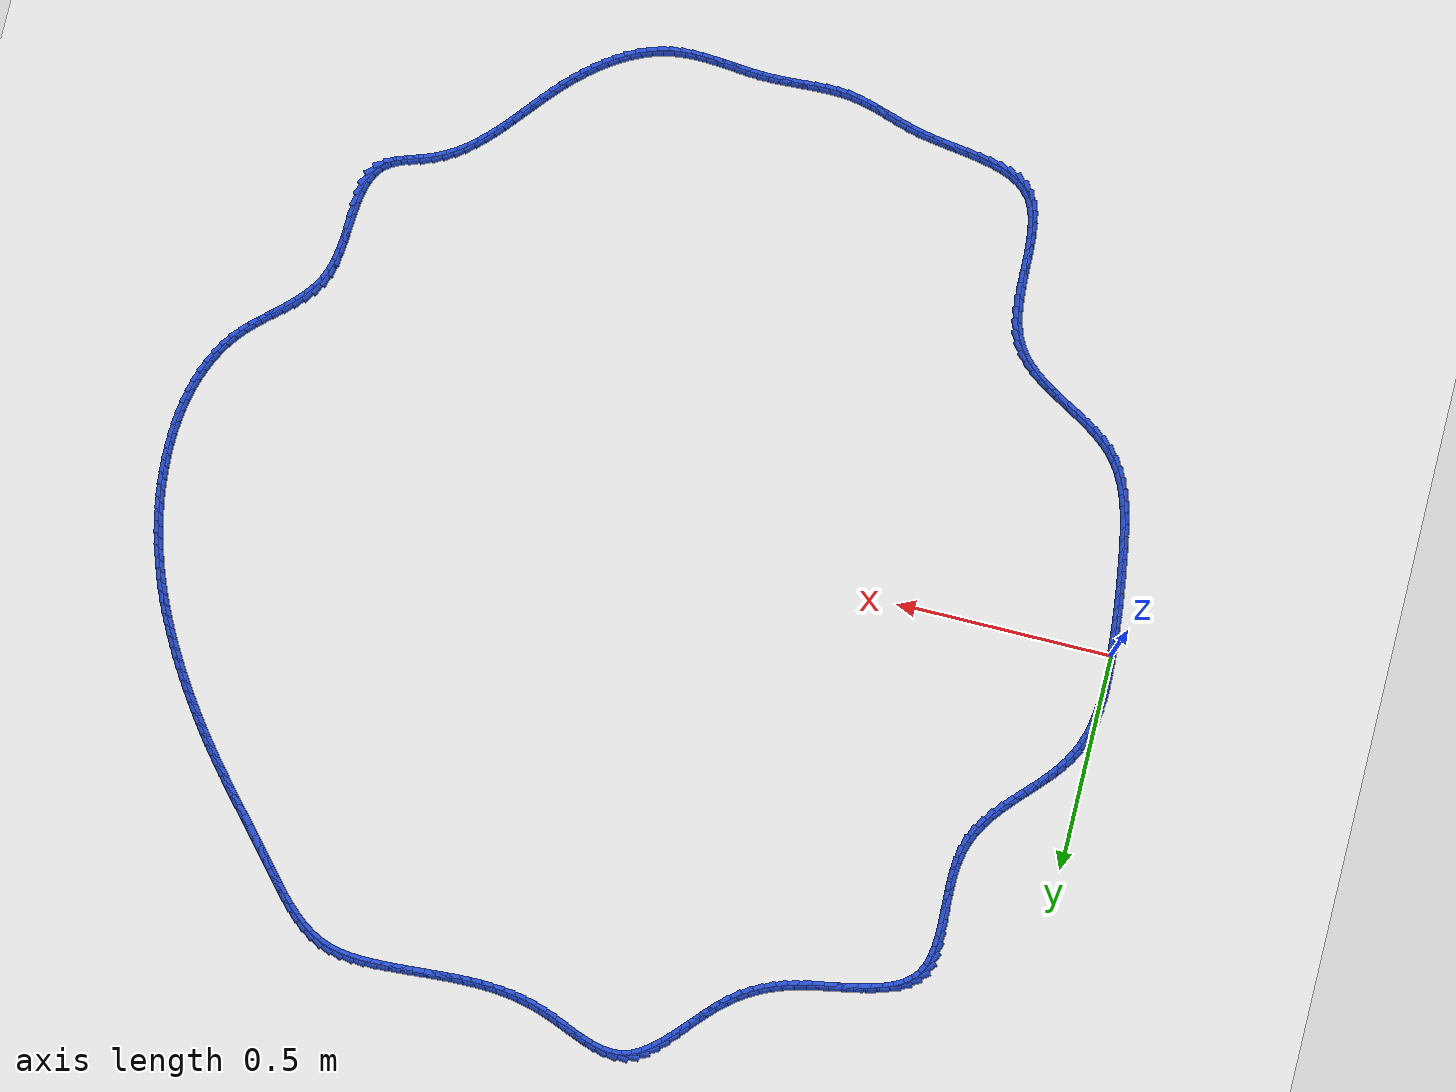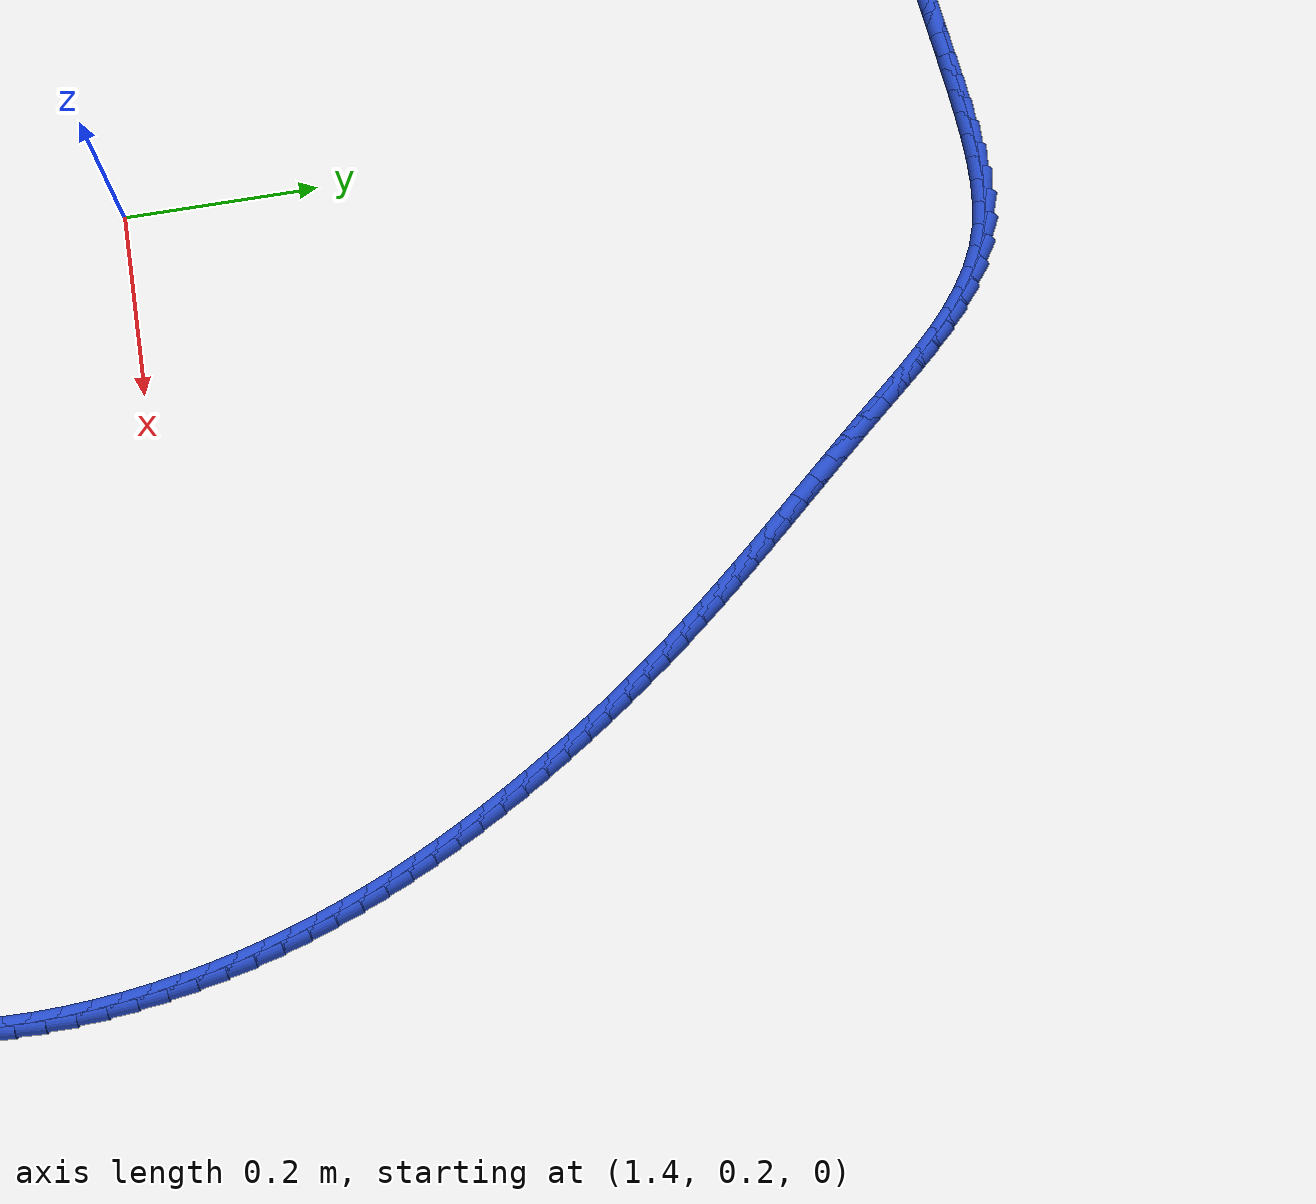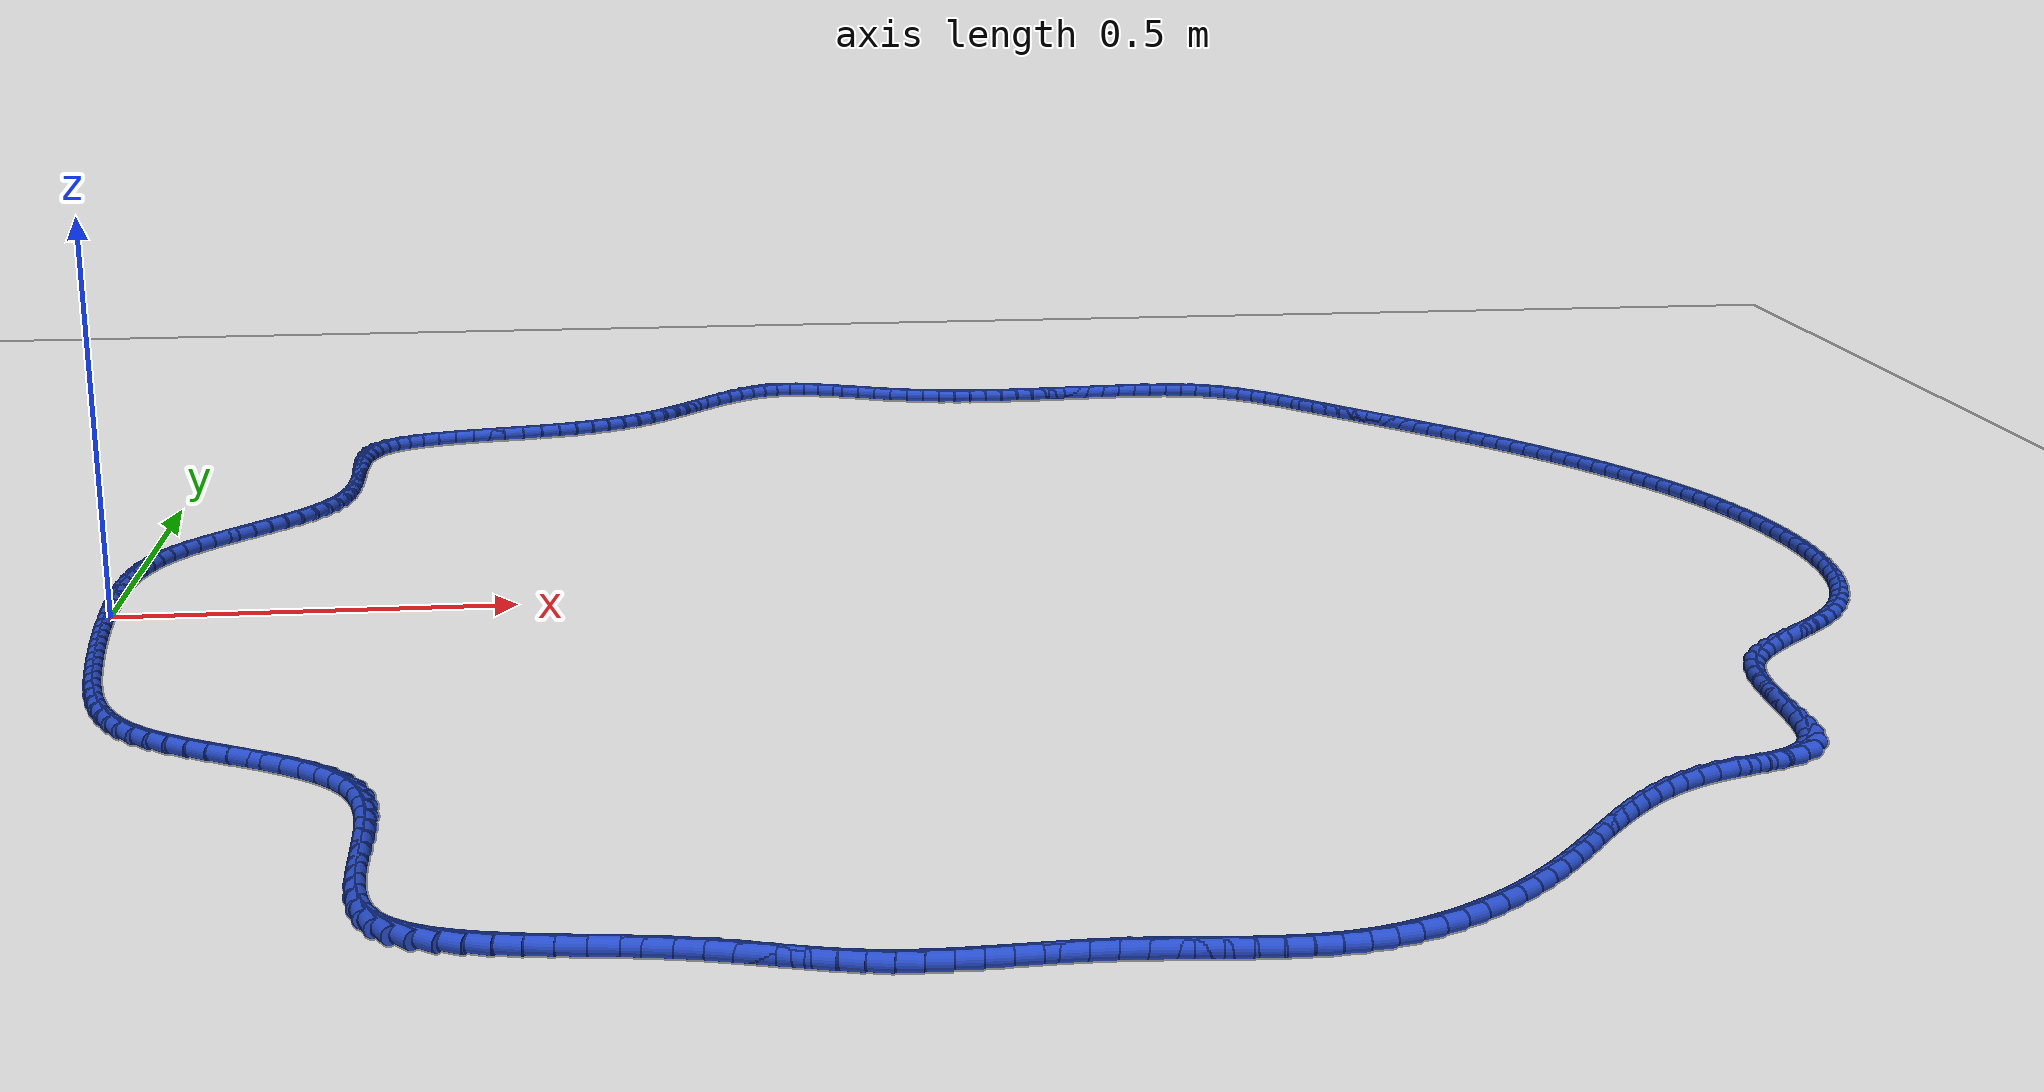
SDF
<sdf version="1.6">
 <world name="default">
  <light name="sun" type="directional">
   <pose>0 0 10 0 -0 0</pose>
   <diffuse>0.8 0.8 0.8 1</diffuse>
   <specular>0.2 0.2 0.2 1</specular>
   <attenuation>
    <range>1000</range>
    <constant>0.9</constant>
    <linear>0.01</linear>
    <quadratic>0.001</quadratic>
   </attenuation>
   <direction>-0.5 0.1 -0.9</direction>
  </light>
  <model name="ground_plane">
   <static>1</static>
   <link name="link">
    <collision name="collision">
     <geometry><plane><normal>0 0 1</normal><size>100 100</size></plane></geometry>
     <surface><friction><ode><mu>100</mu><mu2>50</mu2></ode></friction></surface>
    </collision>
    <visual name="visual">
     <cast_shadows>0</cast_shadows>
     <geometry><plane><normal>0 0 1</normal><size>100 100</size></plane></geometry>
     <material>
      <script><uri>file://media/materials/scripts/gazebo.material</uri><name>Gazebo/WhiteGlow</name></script>
     </material>
    </visual>
   </link>
  </model>
  <gravity>0 0 -9.8</gravity>
  <magnetic_field>6e-06 2.3e-05 -4.2e-05</magnetic_field>
  <atmosphere type="adiabatic"/>
  <physics name="default_physics" default="0" type="ode">
   <max_step_size>0.001</max_step_size>
   <real_time_factor>1</real_time_factor>
   <real_time_update_rate>1000</real_time_update_rate>
  </physics>
  <scene><ambient>0.4 0.4 0.4 1</ambient><background>0.7 0.7 0.7 1</background><shadows>1</shadows></scene>
  <spherical_coordinates>
   <surface_model>EARTH_WGS84</surface_model>
   <latitude_deg>0</latitude_deg>
   <longitude_deg>0</longitude_deg>
   <elevation>0</elevation>
   <heading_deg>0</heading_deg>
  </spherical_coordinates>
  <model name="line">
   <link name="link_0">
    <pose>-4.336808689942018e-19 6.245004513516506e-17 0.01 0 1.57 -1.5156632983631286</pose>
    <collision name="collision">
     <geometry><cylinder><radius>0.01</radius><length>0.08</length></cylinder></geometry>
    </collision>
    <visual name="visual">
     <material>
      <script><name>Gazebo/Blue</name><uri>file://media/materials/scripts/gazebo.material</uri></script>
     </material>
     <geometry><cylinder><radius>0.01</radius><length>0.08</length></cylinder></geometry>
    </visual>
   </link>
   <link name="link_1">
    <pose>-0.0014851051270144866 0.026909461180126652 0.01 0 1.57 -1.5373575224814657</pose>
    <collision name="collision">
     <geometry><cylinder><radius>0.01</radius><length>0.08</length></cylinder></geometry>
    </collision>
    <visual name="visual">
     <material>
      <script><name>Gazebo/Blue</name><uri>file://media/materials/scripts/gazebo.material</uri></script>
     </material>
     <geometry><cylinder><radius>0.01</radius><length>0.08</length></cylinder></geometry>
    </visual>
   </link>
   <link name="link_2">
    <pose>-0.002392326421066504 0.05403014177466341 0.01 0 1.57 -1.568052936660617</pose>
    <collision name="collision">
     <geometry><cylinder><radius>0.01</radius><length>0.08</length></cylinder></geometry>
    </collision>
    <visual name="visual">
     <material>
      <script><name>Gazebo/Blue</name><uri>file://media/materials/scripts/gazebo.material</uri></script>
     </material>
     <geometry><cylinder><radius>0.01</radius><length>0.08</length></cylinder></geometry>
    </visual>
   </link>
   <link name="link_3">
    <pose>-0.0024668079049037423 0.08117950564112851 0.01 0 1.57 1.5332849393124606</pose>
    <collision name="collision">
     <geometry><cylinder><radius>0.01</radius><length>0.08</length></cylinder></geometry>
    </collision>
    <visual name="visual">
     <material>
      <script><name>Gazebo/Blue</name><uri>file://media/materials/scripts/gazebo.material</uri></script>
     </material>
     <geometry><cylinder><radius>0.01</radius><length>0.08</length></cylinder></geometry>
    </visual>
   </link>
   <link name="link_4">
    <pose>-0.0014536936012738838 0.10817501663704009 0.01 0 1.57 1.4826664757514716</pose>
    <collision name="collision">
     <geometry><cylinder><radius>0.01</radius><length>0.08</length></cylinder></geometry>
    </collision>
    <visual name="visual">
     <material>
      <script><name>Gazebo/Blue</name><uri>file://media/materials/scripts/gazebo.material</uri></script>
     </material>
     <geometry><cylinder><radius>0.01</radius><length>0.08</length></cylinder></geometry>
    </visual>
   </link>
   <link name="link_5">
    <pose>0.0009018724670753833 0.13483413861991633 0.01 0 1.57 1.4207151878187974</pose>
    <collision name="collision">
     <geometry><cylinder><radius>0.01</radius><length>0.08</length></cylinder></geometry>
    </collision>
    <visual name="visual">
     <material>
      <script><name>Gazebo/Blue</name><uri>file://media/materials/scripts/gazebo.material</uri></script>
     </material>
     <geometry><cylinder><radius>0.01</radius><length>0.08</length></cylinder></geometry>
    </visual>
   </link>
   <link name="link_6">
    <pose>0.004854746277396374 0.16097433544727544 0.01 0 1.57 1.346441234485536</pose>
    <collision name="collision">
     <geometry><cylinder><radius>0.01</radius><length>0.08</length></cylinder></geometry>
    </collision>
    <visual name="visual">
     <material>
      <script><name>Gazebo/Blue</name><uri>file://media/materials/scripts/gazebo.material</uri></script>
     </material>
     <geometry><cylinder><radius>0.01</radius><length>0.08</length></cylinder></geometry>
    </visual>
   </link>
   <link name="link_7">
    <pose>0.010659783806941402 0.18641307097663556 0.01 0 1.57 1.2590798046489646</pose>
    <collision name="collision">
     <geometry><cylinder><radius>0.01</radius><length>0.08</length></cylinder></geometry>
    </collision>
    <visual name="visual">
     <material>
      <script><name>Gazebo/Blue</name><uri>file://media/materials/scripts/gazebo.material</uri></script>
     </material>
     <geometry><cylinder><radius>0.01</radius><length>0.08</length></cylinder></geometry>
    </visual>
   </link>
   <link name="link_8">
    <pose>0.018571841032962777 0.21096780906551488 0.01 0 1.57 1.158487399252062</pose>
    <collision name="collision">
     <geometry><cylinder><radius>0.01</radius><length>0.08</length></cylinder></geometry>
    </collision>
    <visual name="visual">
     <material>
      <script><name>Gazebo/Blue</name><uri>file://media/materials/scripts/gazebo.material</uri></script>
     </material>
     <geometry><cylinder><radius>0.01</radius><length>0.08</length></cylinder></geometry>
    </visual>
   </link>
   <link name="link_9">
    <pose>0.02884522732654676 0.23445632786346263 0.01 0 1.57 1.0538312243008625</pose>
    <collision name="collision">
     <geometry><cylinder><radius>0.01</radius><length>0.08</length></cylinder></geometry>
    </collision>
    <visual name="visual">
     <material>
      <script><name>Gazebo/Blue</name><uri>file://media/materials/scripts/gazebo.material</uri></script>
     </material>
     <geometry><cylinder><radius>0.01</radius><length>0.08</length></cylinder></geometry>
    </visual>
   </link>
   <link name="link_10">
    <pose>0.04154985769534978 0.25680243008141457 0.01 0 1.57 0.9669070061304351</pose>
    <collision name="collision">
     <geometry><cylinder><radius>0.01</radius><length>0.08</length></cylinder></geometry>
    </collision>
    <visual name="visual">
     <material>
      <script><name>Gazebo/Blue</name><uri>file://media/materials/scripts/gazebo.material</uri></script>
     </material>
     <geometry><cylinder><radius>0.01</radius><length>0.08</length></cylinder></geometry>
    </visual>
   </link>
   <link name="link_11">
    <pose>0.056304039669238616 0.2781895873478418 0.01 0 1.57 0.9009876681101289</pose>
    <collision name="collision">
     <geometry><cylinder><radius>0.01</radius><length>0.08</length></cylinder></geometry>
    </collision>
    <visual name="visual">
     <material>
      <script><name>Gazebo/Blue</name><uri>file://media/materials/scripts/gazebo.material</uri></script>
     </material>
     <geometry><cylinder><radius>0.01</radius><length>0.08</length></cylinder></geometry>
    </visual>
   </link>
   <link name="link_12">
    <pose>0.07265821650890927 0.29884029243719196 0.01 0 1.57 0.8552110789631999</pose>
    <collision name="collision">
     <geometry><cylinder><radius>0.01</radius><length>0.08</length></cylinder></geometry>
    </collision>
    <visual name="visual">
     <material>
      <script><name>Gazebo/Blue</name><uri>file://media/materials/scripts/gazebo.material</uri></script>
     </material>
     <geometry><cylinder><radius>0.01</radius><length>0.08</length></cylinder></geometry>
    </visual>
   </link>
   <link name="link_13">
    <pose>0.09016283147505781 0.3189770381239125 0.01 0 1.57 0.8284661091328717</pose>
    <collision name="collision">
     <geometry><cylinder><radius>0.01</radius><length>0.08</length></cylinder></geometry>
    </collision>
    <visual name="visual">
     <material>
      <script><name>Gazebo/Blue</name><uri>file://media/materials/scripts/gazebo.material</uri></script>
     </material>
     <geometry><cylinder><radius>0.01</radius><length>0.08</length></cylinder></geometry>
    </visual>
   </link>
   <link name="link_14">
    <pose>0.10836832782838036 0.3388223171824514 0.01 0 1.57 0.8198960152028433</pose>
    <collision name="collision">
     <geometry><cylinder><radius>0.01</radius><length>0.08</length></cylinder></geometry>
    </collision>
    <visual name="visual">
     <material>
      <script><name>Gazebo/Blue</name><uri>file://media/materials/scripts/gazebo.material</uri></script>
     </material>
     <geometry><cylinder><radius>0.01</radius><length>0.08</length></cylinder></geometry>
    </visual>
   </link>
   <link name="link_15">
    <pose>0.12682514882957285 0.358598622387256 0.01 0 1.57 0.8291331446700129</pose>
    <collision name="collision">
     <geometry><cylinder><radius>0.01</radius><length>0.08</length></cylinder></geometry>
    </collision>
    <visual name="visual">
     <material>
      <script><name>Gazebo/Blue</name><uri>file://media/materials/scripts/gazebo.material</uri></script>
     </material>
     <geometry><cylinder><radius>0.01</radius><length>0.08</length></cylinder></geometry>
    </visual>
   </link>
   <link name="link_16">
    <pose>0.14508373773933134 0.37852844651277384 0.01 0 1.57 0.8563567514031817</pose>
    <collision name="collision">
     <geometry><cylinder><radius>0.01</radius><length>0.08</length></cylinder></geometry>
    </collision>
    <visual name="visual">
     <material>
      <script><name>Gazebo/Blue</name><uri>file://media/materials/scripts/gazebo.material</uri></script>
     </material>
     <geometry><cylinder><radius>0.01</radius><length>0.08</length></cylinder></geometry>
    </visual>
   </link>
   <link name="link_17">
    <pose>0.162694537818352 0.39883428233345286 0.01 0 1.57 0.9022114575777578</pose>
    <collision name="collision">
     <geometry><cylinder><radius>0.01</radius><length>0.08</length></cylinder></geometry>
    </collision>
    <visual name="visual">
     <material>
      <script><name>Gazebo/Blue</name><uri>file://media/materials/scripts/gazebo.material</uri></script>
     </material>
     <geometry><cylinder><radius>0.01</radius><length>0.08</length></cylinder></geometry>
    </visual>
   </link>
   <link name="link_18">
    <pose>0.17920799232733065 0.41973862262374023 0.01 0 1.57 0.9675599634669823</pose>
    <collision name="collision">
     <geometry><cylinder><radius>0.01</radius><length>0.08</length></cylinder></geometry>
    </collision>
    <visual name="visual">
     <material>
      <script><name>Gazebo/Blue</name><uri>file://media/materials/scripts/gazebo.material</uri></script>
     </material>
     <geometry><cylinder><radius>0.01</radius><length>0.08</length></cylinder></geometry>
    </visual>
   </link>
   <link name="link_19">
    <pose>0.19417454452696353 0.44146396015808387 0.01 0 1.57 1.0529976283603883</pose>
    <collision name="collision">
     <geometry><cylinder><radius>0.01</radius><length>0.08</length></cylinder></geometry>
    </collision>
    <visual name="visual">
     <material>
      <script><name>Gazebo/Blue</name><uri>file://media/materials/scripts/gazebo.material</uri></script>
     </material>
     <geometry><cylinder><radius>0.01</radius><length>0.08</length></cylinder></geometry>
    </visual>
   </link>
   <link name="link_20">
    <pose>0.2071446376779466 0.46423278771093135 0.01 0 1.57 1.1580769425891473</pose>
    <collision name="collision">
     <geometry><cylinder><radius>0.01</radius><length>0.08</length></cylinder></geometry>
    </collision>
    <visual name="visual">
     <material>
      <script><name>Gazebo/Blue</name><uri>file://media/materials/scripts/gazebo.material</uri></script>
     </material>
     <geometry><cylinder><radius>0.01</radius><length>0.08</length></cylinder></geometry>
    </visual>
   </link>
   <link name="link_21">
    <pose>0.217668715040976 0.48826759805673037 0.01 0 1.57 1.2801264135120118</pose>
    <collision name="collision">
     <geometry><cylinder><radius>0.01</radius><length>0.08</length></cylinder></geometry>
    </collision>
    <visual name="visual">
     <material>
      <script><name>Gazebo/Blue</name><uri>file://media/materials/scripts/gazebo.material</uri></script>
     </material>
     <geometry><cylinder><radius>0.01</radius><length>0.08</length></cylinder></geometry>
    </visual>
   </link>
   <link name="link_22">
    <pose>0.22530283574739954 0.5137876116351567 0.01 0 1.57 1.3988331664665183</pose>
    <collision name="collision">
     <geometry><cylinder><radius>0.01</radius><length>0.08</length></cylinder></geometry>
    </collision>
    <visual name="visual">
     <material>
      <script><name>Gazebo/Blue</name><uri>file://media/materials/scripts/gazebo.material</uri></script>
     </material>
     <geometry><cylinder><radius>0.01</radius><length>0.08</length></cylinder></geometry>
    </visual>
   </link>
   <link name="link_23">
    <pose>0.22999179488485705 0.5407855347323979 0.01 0 1.57 1.4883130044301487</pose>
    <collision name="collision">
     <geometry><cylinder><radius>0.01</radius><length>0.08</length></cylinder></geometry>
    </collision>
    <visual name="visual">
     <material>
      <script><name>Gazebo/Blue</name><uri>file://media/materials/scripts/gazebo.material</uri></script>
     </material>
     <geometry><cylinder><radius>0.01</radius><length>0.08</length></cylinder></geometry>
    </visual>
   </link>
   <link name="link_24">
    <pose>0.23231475568571194 0.5688844310508364 0.01 0 1.57 1.5501457131390552</pose>
    <collision name="collision">
     <geometry><cylinder><radius>0.01</radius><length>0.08</length></cylinder></geometry>
    </collision>
    <visual name="visual">
     <material>
      <script><name>Gazebo/Blue</name><uri>file://media/materials/scripts/gazebo.material</uri></script>
     </material>
     <geometry><cylinder><radius>0.01</radius><length>0.08</length></cylinder></geometry>
    </visual>
   </link>
   <link name="link_25">
    <pose>0.2329093479402196 0.5976732961737259 0.01 0 1.57 -1.553729406542433</pose>
    <collision name="collision">
     <geometry><cylinder><radius>0.01</radius><length>0.08</length></cylinder></geometry>
    </collision>
    <visual name="visual">
     <material>
      <script><name>Gazebo/Blue</name><uri>file://media/materials/scripts/gazebo.material</uri></script>
     </material>
     <geometry><cylinder><radius>0.01</radius><length>0.08</length></cylinder></geometry>
    </visual>
   </link>
   <link name="link_26">
    <pose>0.2324132014386355 0.6267411256843207 0.01 0 1.57 -1.5380025039007692</pose>
    <collision name="collision">
     <geometry><cylinder><radius>0.01</radius><length>0.08</length></cylinder></geometry>
    </collision>
    <visual name="visual">
     <material>
      <script><name>Gazebo/Blue</name><uri>file://media/materials/scripts/gazebo.material</uri></script>
     </material>
     <geometry><cylinder><radius>0.01</radius><length>0.08</length></cylinder></geometry>
    </visual>
   </link>
   <link name="link_27">
    <pose>0.2314639459712151 0.6556769151658748 0.01 0 1.57 -1.5438686804115205</pose>
    <collision name="collision">
     <geometry><cylinder><radius>0.01</radius><length>0.08</length></cylinder></geometry>
    </collision>
    <visual name="visual">
     <material>
      <script><name>Gazebo/Blue</name><uri>file://media/materials/scripts/gazebo.material</uri></script>
     </material>
     <geometry><cylinder><radius>0.01</radius><length>0.08</length></cylinder></geometry>
    </visual>
   </link>
   <link name="link_28">
    <pose>0.23069921132821403 0.6840696602016425 0.01 0 1.57 1.5687038116290828</pose>
    <collision name="collision">
     <geometry><cylinder><radius>0.01</radius><length>0.08</length></cylinder></geometry>
    </collision>
    <visual name="visual">
     <material>
      <script><name>Gazebo/Blue</name><uri>file://media/materials/scripts/gazebo.material</uri></script>
     </material>
     <geometry><cylinder><radius>0.01</radius><length>0.08</length></cylinder></geometry>
    </visual>
   </link>
   <link name="link_29">
    <pose>0.2307566272998876 0.7115083563748775 0.01 0 1.57 1.5126729770589935</pose>
    <collision name="collision">
     <geometry><cylinder><radius>0.01</radius><length>0.08</length></cylinder></geometry>
    </collision>
    <visual name="visual">
     <material>
      <script><name>Gazebo/Blue</name><uri>file://media/materials/scripts/gazebo.material</uri></script>
     </material>
     <geometry><cylinder><radius>0.01</radius><length>0.08</length></cylinder></geometry>
    </visual>
   </link>
   <link name="link_30">
    <pose>0.23227382367649135 0.737581999268834 0.01 0 1.57 1.4231153753150907</pose>
    <collision name="collision">
     <geometry><cylinder><radius>0.01</radius><length>0.08</length></cylinder></geometry>
    </collision>
    <visual name="visual">
     <material>
      <script><name>Gazebo/Blue</name><uri>file://media/materials/scripts/gazebo.material</uri></script>
     </material>
     <geometry><cylinder><radius>0.01</radius><length>0.08</length></cylinder></geometry>
    </visual>
   </link>
   <link name="link_31">
    <pose>0.23588843024828074 0.7618795844667661 0.01 0 1.57 1.2911443324672314</pose>
    <collision name="collision">
     <geometry><cylinder><radius>0.01</radius><length>0.08</length></cylinder></geometry>
    </collision>
    <visual name="visual">
     <material>
      <script><name>Gazebo/Blue</name><uri>file://media/materials/scripts/gazebo.material</uri></script>
     </material>
     <geometry><cylinder><radius>0.01</radius><length>0.08</length></cylinder></geometry>
    </visual>
   </link>
   <link name="link_32">
    <pose>0.2422380768055113 0.7839901075519278 0.01 0 1.57 1.1085400552464884</pose>
    <collision name="collision">
     <geometry><cylinder><radius>0.01</radius><length>0.08</length></cylinder></geometry>
    </collision>
    <visual name="visual">
     <material>
      <script><name>Gazebo/Blue</name><uri>file://media/materials/scripts/gazebo.material</uri></script>
     </material>
     <geometry><cylinder><radius>0.01</radius><length>0.08</length></cylinder></geometry>
    </visual>
   </link>
   <link name="link_33">
    <pose>0.25196039313843843 0.8035025641075734 0.01 0 1.57 0.8814031383299049</pose>
    <collision name="collision">
     <geometry><cylinder><radius>0.01</radius><length>0.08</length></cylinder></geometry>
    </collision>
    <visual name="visual">
     <material>
      <script><name>Gazebo/Blue</name><uri>file://media/materials/scripts/gazebo.material</uri></script>
     </material>
     <geometry><cylinder><radius>0.01</radius><length>0.08</length></cylinder></geometry>
    </visual>
   </link>
   <link name="link_34">
    <pose>0.2656116137168598 0.8200632192654634 0.01 0 1.57 0.6683258235549239</pose>
    <collision name="collision">
     <geometry><cylinder><radius>0.01</radius><length>0.08</length></cylinder></geometry>
    </collision>
    <visual name="visual">
     <material>
      <script><name>Gazebo/Blue</name><uri>file://media/materials/scripts/gazebo.material</uri></script>
     </material>
     <geometry><cylinder><radius>0.01</radius><length>0.08</length></cylinder></geometry>
    </visual>
   </link>
   <link name="link_35">
    <pose>0.2830352882135735 0.8338197814384 0.01 0 1.57 0.5024953430491619</pose>
    <collision name="collision">
     <geometry><cylinder><radius>0.01</radius><length>0.08</length></cylinder></geometry>
    </collision>
    <visual name="visual">
     <material>
      <script><name>Gazebo/Blue</name><uri>file://media/materials/scripts/gazebo.material</uri></script>
     </material>
     <geometry><cylinder><radius>0.01</radius><length>0.08</length></cylinder></geometry>
    </visual>
   </link>
   <link name="link_36">
    <pose>0.30370620266704607 0.8451794202308732 0.01 0 1.57 0.38110081155639564</pose>
    <collision name="collision">
     <geometry><cylinder><radius>0.01</radius><length>0.08</length></cylinder></geometry>
    </collision>
    <visual name="visual">
     <material>
      <script><name>Gazebo/Blue</name><uri>file://media/materials/scripts/gazebo.material</uri></script>
     </material>
     <geometry><cylinder><radius>0.01</radius><length>0.08</length></cylinder></geometry>
    </visual>
   </link>
   <link name="link_37">
    <pose>0.3270960411494506 0.8545514877832754 0.01 0 1.57 0.29574475086381513</pose>
    <collision name="collision">
     <geometry><cylinder><radius>0.01</radius><length>0.08</length></cylinder></geometry>
    </collision>
    <visual name="visual">
     <material>
      <script><name>Gazebo/Blue</name><uri>file://media/materials/scripts/gazebo.material</uri></script>
     </material>
     <geometry><cylinder><radius>0.01</radius><length>0.08</length></cylinder></geometry>
    </visual>
   </link>
   <link name="link_38">
    <pose>0.3526764877329599 0.8623453362359983 0.01 0 1.57 0.2385528095769914</pose>
    <collision name="collision">
     <geometry><cylinder><radius>0.01</radius><length>0.08</length></cylinder></geometry>
    </collision>
    <visual name="visual">
     <material>
      <script><name>Gazebo/Blue</name><uri>file://media/materials/scripts/gazebo.material</uri></script>
     </material>
     <geometry><cylinder><radius>0.01</radius><length>0.08</length></cylinder></geometry>
    </visual>
   </link>
   <link name="link_39">
    <pose>0.37991922648974713 0.868970317729434 0.01 0 1.57 0.2038294780840506</pose>
    <collision name="collision">
     <geometry><cylinder><radius>0.01</radius><length>0.08</length></cylinder></geometry>
    </collision>
    <visual name="visual">
     <material>
      <script><name>Gazebo/Blue</name><uri>file://media/materials/scripts/gazebo.material</uri></script>
     </material>
     <geometry><cylinder><radius>0.01</radius><length>0.08</length></cylinder></geometry>
    </visual>
   </link>
   <link name="link_40">
    <pose>0.4082959414919849 0.8748357844039745 0.01 0 1.57 0.18805007849693478</pose>
    <collision name="collision">
     <geometry><cylinder><radius>0.01</radius><length>0.08</length></cylinder></geometry>
    </collision>
    <visual name="visual">
     <material>
      <script><name>Gazebo/Blue</name><uri>file://media/materials/scripts/gazebo.material</uri></script>
     </material>
     <geometry><cylinder><radius>0.01</radius><length>0.08</length></cylinder></geometry>
    </visual>
   </link>
   <link name="link_41">
    <pose>0.4372783168118466 0.8803510884000115 0.01 0 1.57 0.18952650978616276</pose>
    <collision name="collision">
     <geometry><cylinder><radius>0.01</radius><length>0.08</length></cylinder></geometry>
    </collision>
    <visual name="visual">
     <material>
      <script><name>Gazebo/Blue</name><uri>file://media/materials/scripts/gazebo.material</uri></script>
     </material>
     <geometry><cylinder><radius>0.01</radius><length>0.08</length></cylinder></geometry>
    </visual>
   </link>
   <link name="link_42">
    <pose>0.4663380365215052 0.8859255818579378 0.01 0 1.57 0.20817025769582292</pose>
    <collision name="collision">
     <geometry><cylinder><radius>0.01</radius><length>0.08</length></cylinder></geometry>
    </collision>
    <visual name="visual">
     <material>
      <script><name>Gazebo/Blue</name><uri>file://media/materials/scripts/gazebo.material</uri></script>
     </material>
     <geometry><cylinder><radius>0.01</radius><length>0.08</length></cylinder></geometry>
    </visual>
   </link>
   <link name="link_43">
    <pose>0.49494678469313347 0.8919686169181444 0.01 0 1.57 0.24544051459341526</pose>
    <collision name="collision">
     <geometry><cylinder><radius>0.01</radius><length>0.08</length></cylinder></geometry>
    </collision>
    <visual name="visual">
     <material>
      <script><name>Gazebo/Blue</name><uri>file://media/materials/scripts/gazebo.material</uri></script>
     </material>
     <geometry><cylinder><radius>0.01</radius><length>0.08</length></cylinder></geometry>
    </visual>
   </link>
   <link name="link_44">
    <pose>0.5225762509966341 0.8988895433145175 0.01 0 1.57 0.30126496781764067</pose>
    <collision name="collision">
     <geometry><cylinder><radius>0.01</radius><length>0.08</length></cylinder></geometry>
    </collision>
    <visual name="visual">
     <material>
      <script><name>Gazebo/Blue</name><uri>file://media/materials/scripts/gazebo.material</uri></script>
     </material>
     <geometry><cylinder><radius>0.01</radius><length>0.08</length></cylinder></geometry>
    </visual>
   </link>
   <link name="link_45">
    <pose>0.5488216759274406 0.9070445953444581 0.01 0 1.57 0.36642740367754484</pose>
    <collision name="collision">
     <geometry><cylinder><radius>0.01</radius><length>0.08</length></cylinder></geometry>
    </collision>
    <visual name="visual">
     <material>
      <script><name>Gazebo/Blue</name><uri>file://media/materials/scripts/gazebo.material</uri></script>
     </material>
     <geometry><cylinder><radius>0.01</radius><length>0.08</length></cylinder></geometry>
    </visual>
   </link>
   <link name="link_46">
    <pose>0.5737207020875215 0.916599815286096 0.01 0 1.57 0.4374550515494316</pose>
    <collision name="collision">
     <geometry><cylinder><radius>0.01</radius><length>0.08</length></cylinder></geometry>
    </collision>
    <visual name="visual">
     <material>
      <script><name>Gazebo/Blue</name><uri>file://media/materials/scripts/gazebo.material</uri></script>
     </material>
     <geometry><cylinder><radius>0.01</radius><length>0.08</length></cylinder></geometry>
    </visual>
   </link>
   <link name="link_47">
    <pose>0.5974099544098117 0.9276786921631349 0.01 0 1.57 0.5125394096000014</pose>
    <collision name="collision">
     <geometry><cylinder><radius>0.01</radius><length>0.08</length></cylinder></geometry>
    </collision>
    <visual name="visual">
     <material>
      <script><name>Gazebo/Blue</name><uri>file://media/materials/scripts/gazebo.material</uri></script>
     </material>
     <geometry><cylinder><radius>0.01</radius><length>0.08</length></cylinder></geometry>
    </visual>
   </link>
   <link name="link_48">
    <pose>0.6200260578272451 0.9404047149992777 0.01 0 1.57 0.589393772578855</pose>
    <collision name="collision">
     <geometry><cylinder><radius>0.01</radius><length>0.08</length></cylinder></geometry>
    </collision>
    <visual name="visual">
     <material>
      <script><name>Gazebo/Blue</name><uri>file://media/materials/scripts/gazebo.material</uri></script>
     </material>
     <geometry><cylinder><radius>0.01</radius><length>0.08</length></cylinder></geometry>
    </visual>
   </link>
   <link name="link_49">
    <pose>0.6417056372727566 0.9549013728182282 0.01 0 1.57 0.6655343394546928</pose>
    <collision name="collision">
     <geometry><cylinder><radius>0.01</radius><length>0.08</length></cylinder></geometry>
    </collision>
    <visual name="visual">
     <material>
      <script><name>Gazebo/Blue</name><uri>file://media/materials/scripts/gazebo.material</uri></script>
     </material>
     <geometry><cylinder><radius>0.01</radius><length>0.08</length></cylinder></geometry>
    </visual>
   </link>
   <link name="link_50">
    <pose>0.66258531767928 0.9712921546436889 0.01 0 1.57 0.738272810275782</pose>
    <collision name="collision">
     <geometry><cylinder><radius>0.01</radius><length>0.08</length></cylinder></geometry>
    </collision>
    <visual name="visual">
     <material>
      <script><name>Gazebo/Blue</name><uri>file://media/materials/scripts/gazebo.material</uri></script>
     </material>
     <geometry><cylinder><radius>0.01</radius><length>0.08</length></cylinder></geometry>
    </visual>
   </link>
   <link name="link_51">
    <pose>0.6828022919840575 0.989688131755414 0.01 0 1.57 0.795839715297439</pose>
    <collision name="collision">
     <geometry><cylinder><radius>0.01</radius><length>0.08</length></cylinder></geometry>
    </collision>
    <visual name="visual">
     <material>
      <script><name>Gazebo/Blue</name><uri>file://media/materials/scripts/gazebo.material</uri></script>
     </material>
     <geometry><cylinder><radius>0.01</radius><length>0.08</length></cylinder></geometry>
    </visual>
   </link>
   <link name="link_52">
    <pose>0.702511460875961 1.00981324751435 0.01 0 1.57 0.8285183529158602</pose>
    <collision name="collision">
     <geometry><cylinder><radius>0.01</radius><length>0.08</length></cylinder></geometry>
    </collision>
    <visual name="visual">
     <material>
      <script><name>Gazebo/Blue</name><uri>file://media/materials/scripts/gazebo.material</uri></script>
     </material>
     <geometry><cylinder><radius>0.01</radius><length>0.08</length></cylinder></geometry>
    </visual>
   </link>
   <link name="link_53">
    <pose>0.7218884762774764 1.03093778057853 0.01 0 1.57 0.8382363117363955</pose>
    <collision name="collision">
     <geometry><cylinder><radius>0.01</radius><length>0.08</length></cylinder></geometry>
    </collision>
    <visual name="visual">
     <material>
      <script><name>Gazebo/Blue</name><uri>file://media/materials/scripts/gazebo.material</uri></script>
     </material>
     <geometry><cylinder><radius>0.01</radius><length>0.08</length></cylinder></geometry>
    </visual>
   </link>
   <link name="link_54">
    <pose>0.7411101716157126 1.0523061794816884 0.01 0 1.57 0.8256135696002049</pose>
    <collision name="collision">
     <geometry><cylinder><radius>0.01</radius><length>0.08</length></cylinder></geometry>
    </collision>
    <visual name="visual">
     <material>
      <script><name>Gazebo/Blue</name><uri>file://media/materials/scripts/gazebo.material</uri></script>
     </material>
     <geometry><cylinder><radius>0.01</radius><length>0.08</length></cylinder></geometry>
    </visual>
   </link>
   <link name="link_55">
    <pose>0.7603533803177783 1.0731628927575592 0.01 0 1.57 0.7891879679398328</pose>
    <collision name="collision">
     <geometry><cylinder><radius>0.01</radius><length>0.08</length></cylinder></geometry>
    </collision>
    <visual name="visual">
     <material>
      <script><name>Gazebo/Blue</name><uri>file://media/materials/scripts/gazebo.material</uri></script>
     </material>
     <geometry><cylinder><radius>0.01</radius><length>0.08</length></cylinder></geometry>
    </visual>
   </link>
   <link name="link_56">
    <pose>0.7797949358107827 1.0927523689398775 0.01 0 1.57 0.7252822954863996</pose>
    <collision name="collision">
     <geometry><cylinder><radius>0.01</radius><length>0.08</length></cylinder></geometry>
    </collision>
    <visual name="visual">
     <material>
      <script><name>Gazebo/Blue</name><uri>file://media/materials/scripts/gazebo.material</uri></script>
     </material>
     <geometry><cylinder><radius>0.01</radius><length>0.08</length></cylinder></geometry>
    </visual>
   </link>
   <link name="link_57">
    <pose>0.7996116715218343 1.1103190565623773 0.01 0 1.57 0.6279837827026062</pose>
    <collision name="collision">
     <geometry><cylinder><radius>0.01</radius><length>0.08</length></cylinder></geometry>
    </collision>
    <visual name="visual">
     <material>
      <script><name>Gazebo/Blue</name><uri>file://media/materials/scripts/gazebo.material</uri></script>
     </material>
     <geometry><cylinder><radius>0.01</radius><length>0.08</length></cylinder></geometry>
    </visual>
   </link>
   <link name="link_58">
    <pose>0.8199804208780425 1.1251074041587927 0.01 0 1.57 0.4900460597568495</pose>
    <collision name="collision">
     <geometry><cylinder><radius>0.01</radius><length>0.08</length></cylinder></geometry>
    </collision>
    <visual name="visual">
     <material>
      <script><name>Gazebo/Blue</name><uri>file://media/materials/scripts/gazebo.material</uri></script>
     </material>
     <geometry><cylinder><radius>0.01</radius><length>0.08</length></cylinder></geometry>
    </visual>
   </link>
   <link name="link_59">
    <pose>0.8410780173065158 1.1363618602628585 0.01 0 1.57 0.3065651528894308</pose>
    <collision name="collision">
     <geometry><cylinder><radius>0.01</radius><length>0.08</length></cylinder></geometry>
    </collision>
    <visual name="visual">
     <material>
      <script><name>Gazebo/Blue</name><uri>file://media/materials/scripts/gazebo.material</uri></script>
     </material>
     <geometry><cylinder><radius>0.01</radius><length>0.08</length></cylinder></geometry>
    </visual>
   </link>
   <link name="link_60">
    <pose>0.8630812942343626 1.1433268734083086 0.01 0 1.57 0.09086140304876274</pose>
    <collision name="collision">
     <geometry><cylinder><radius>0.01</radius><length>0.08</length></cylinder></geometry>
    </collision>
    <visual name="visual">
     <material>
      <script><name>Gazebo/Blue</name><uri>file://media/materials/scripts/gazebo.material</uri></script>
     </material>
     <geometry><cylinder><radius>0.01</radius><length>0.08</length></cylinder></geometry>
    </visual>
   </link>
   <link name="link_61">
    <pose>0.8861306450218375 1.1454269522166274 0.01 0 1.57 -0.09375971632706391</pose>
    <collision name="collision">
     <geometry><cylinder><radius>0.01</radius><length>0.08</length></cylinder></geometry>
    </collision>
    <visual name="visual">
     <material>
      <script><name>Gazebo/Blue</name><uri>file://media/materials/scripts/gazebo.material</uri></script>
     </material>
     <geometry><cylinder><radius>0.01</radius><length>0.08</length></cylinder></geometry>
    </visual>
   </link>
   <link name="link_62">
    <pose>0.9101475088881974 1.1431685161081426 0.01 0 1.57 -0.22601905792737412</pose>
    <collision name="collision">
     <geometry><cylinder><radius>0.01</radius><length>0.08</length></cylinder></geometry>
    </collision>
    <visual name="visual">
     <material>
      <script><name>Gazebo/Blue</name><uri>file://media/materials/scripts/gazebo.material</uri></script>
     </material>
     <geometry><cylinder><radius>0.01</radius><length>0.08</length></cylinder></geometry>
    </visual>
   </link>
   <link name="link_63">
    <pose>0.9349719279952751 1.1374601890699565 0.01 0 1.57 -0.3131862320692095</pose>
    <collision name="collision">
     <geometry><cylinder><radius>0.01</radius><length>0.08</length></cylinder></geometry>
    </collision>
    <visual name="visual">
     <material>
      <script><name>Gazebo/Blue</name><uri>file://media/materials/scripts/gazebo.material</uri></script>
     </material>
     <geometry><cylinder><radius>0.01</radius><length>0.08</length></cylinder></geometry>
    </visual>
   </link>
   <link name="link_64">
    <pose>0.9604438086678797 1.12921126629612 0.01 0 1.57 -0.36367568333197986</pose>
    <collision name="collision">
     <geometry><cylinder><radius>0.01</radius><length>0.08</length></cylinder></geometry>
    </collision>
    <visual name="visual">
     <material>
      <script><name>Gazebo/Blue</name><uri>file://media/materials/scripts/gazebo.material</uri></script>
     </material>
     <geometry><cylinder><radius>0.01</radius><length>0.08</length></cylinder></geometry>
    </visual>
   </link>
   <link name="link_65">
    <pose>0.9864030572308216 1.119331042980685 0.01 0 1.57 -0.38337656161099104</pose>
    <collision name="collision">
     <geometry><cylinder><radius>0.01</radius><length>0.08</length></cylinder></geometry>
    </collision>
    <visual name="visual">
     <material>
      <script><name>Gazebo/Blue</name><uri>file://media/materials/scripts/gazebo.material</uri></script>
     </material>
     <geometry><cylinder><radius>0.01</radius><length>0.08</length></cylinder></geometry>
    </visual>
   </link>
   <link name="link_66">
    <pose>1.0126895800089102 1.1087288143177032 0.01 0 1.57 -0.3750673628982152</pose>
    <collision name="collision">
     <geometry><cylinder><radius>0.01</radius><length>0.08</length></cylinder></geometry>
    </collision>
    <visual name="visual">
     <material>
      <script><name>Gazebo/Blue</name><uri>file://media/materials/scripts/gazebo.material</uri></script>
     </material>
     <geometry><cylinder><radius>0.01</radius><length>0.08</length></cylinder></geometry>
    </visual>
   </link>
   <link name="link_67">
    <pose>1.0391432833269554 1.0983138755012258 0.01 0 1.57 -0.33860093862001595</pose>
    <collision name="collision">
     <geometry><cylinder><radius>0.01</radius><length>0.08</length></cylinder></geometry>
    </collision>
    <visual name="visual">
     <material>
      <script><name>Gazebo/Blue</name><uri>file://media/materials/scripts/gazebo.material</uri></script>
     </material>
     <geometry><cylinder><radius>0.01</radius><length>0.08</length></cylinder></geometry>
    </visual>
   </link>
   <link name="link_68">
    <pose>1.0656041045142013 1.0889953393041476 0.01 0 1.57 -0.27916170906098564</pose>
    <collision name="collision">
     <geometry><cylinder><radius>0.01</radius><length>0.08</length></cylinder></geometry>
    </collision>
    <visual name="visual">
     <material>
      <script><name>Gazebo/Blue</name><uri>file://media/materials/scripts/gazebo.material</uri></script>
     </material>
     <geometry><cylinder><radius>0.01</radius><length>0.08</length></cylinder></geometry>
    </visual>
   </link>
   <link name="link_69">
    <pose>1.0919527257164268 1.0814425877384994 0.01 0 1.57 -0.2186142378126211</pose>
    <collision name="collision">
     <geometry><cylinder><radius>0.01</radius><length>0.08</length></cylinder></geometry>
    </collision>
    <visual name="visual">
     <material>
      <script><name>Gazebo/Blue</name><uri>file://media/materials/scripts/gazebo.material</uri></script>
     </material>
     <geometry><cylinder><radius>0.01</radius><length>0.08</length></cylinder></geometry>
    </visual>
   </link>
   <link name="link_70">
    <pose>1.118190770663231 1.075613417383474 0.01 0 1.57 -0.16219459571899836</pose>
    <collision name="collision">
     <geometry><cylinder><radius>0.01</radius><length>0.08</length></cylinder></geometry>
    </collision>
    <visual name="visual">
     <material>
      <script><name>Gazebo/Blue</name><uri>file://media/materials/scripts/gazebo.material</uri></script>
     </material>
     <geometry><cylinder><radius>0.01</radius><length>0.08</length></cylinder></geometry>
    </visual>
   </link>
   <link name="link_71">
    <pose>1.1443421990329217 1.0713342065316445 0.01 0 1.57 -0.11081324031563565</pose>
    <collision name="collision">
     <geometry><cylinder><radius>0.01</radius><length>0.08</length></cylinder></geometry>
    </collision>
    <visual name="visual">
     <material>
      <script><name>Gazebo/Blue</name><uri>file://media/materials/scripts/gazebo.material</uri></script>
     </material>
     <geometry><cylinder><radius>0.01</radius><length>0.08</length></cylinder></geometry>
    </visual>
   </link>
   <link name="link_72">
    <pose>1.1704309705038032 1.0684313334755833 0.01 0 1.57 -0.06517252712021358</pose>
    <collision name="collision">
     <geometry><cylinder><radius>0.01</radius><length>0.08</length></cylinder></geometry>
    </collision>
    <visual name="visual">
     <material>
      <script><name>Gazebo/Blue</name><uri>file://media/materials/scripts/gazebo.material</uri></script>
     </material>
     <geometry><cylinder><radius>0.01</radius><length>0.08</length></cylinder></geometry>
    </visual>
   </link>
   <link name="link_73">
    <pose>1.1964810447541816 1.0667311765078633 0.01 0 1.57 -0.025769362839261636</pose>
    <collision name="collision">
     <geometry><cylinder><radius>0.01</radius><length>0.08</length></cylinder></geometry>
    </collision>
    <visual name="visual">
     <material>
      <script><name>Gazebo/Blue</name><uri>file://media/materials/scripts/gazebo.material</uri></script>
     </material>
     <geometry><cylinder><radius>0.01</radius><length>0.08</length></cylinder></geometry>
    </visual>
   </link>
   <link name="link_74">
    <pose>1.2225163814623616 1.0660601139210573 0.01 0 1.57 0.007080442641253311</pose>
    <collision name="collision">
     <geometry><cylinder><radius>0.01</radius><length>0.08</length></cylinder></geometry>
    </collision>
    <visual name="visual">
     <material>
      <script><name>Gazebo/Blue</name><uri>file://media/materials/scripts/gazebo.material</uri></script>
     </material>
     <geometry><cylinder><radius>0.01</radius><length>0.08</length></cylinder></geometry>
    </visual>
   </link>
   <link name="link_75">
    <pose>1.2485609403066493 1.0662445240077378 0.01 0 1.57 0.03320619857169139</pose>
    <collision name="collision">
     <geometry><cylinder><radius>0.01</radius><length>0.08</length></cylinder></geometry>
    </collision>
    <visual name="visual">
     <material>
      <script><name>Gazebo/Blue</name><uri>file://media/materials/scripts/gazebo.material</uri></script>
     </material>
     <geometry><cylinder><radius>0.01</radius><length>0.08</length></cylinder></geometry>
    </visual>
   </link>
   <link name="link_76">
    <pose>1.2746386809653507 1.0671107850604782 0.01 0 1.57 0.052543767030557346</pose>
    <collision name="collision">
     <geometry><cylinder><radius>0.01</radius><length>0.08</length></cylinder></geometry>
    </collision>
    <visual name="visual">
     <material>
      <script><name>Gazebo/Blue</name><uri>file://media/materials/scripts/gazebo.material</uri></script>
     </material>
     <geometry><cylinder><radius>0.01</radius><length>0.08</length></cylinder></geometry>
    </visual>
   </link>
   <link name="link_77">
    <pose>1.3007735631167707 1.0684852753718501 0.01 0 1.57 0.06510084725809813</pose>
    <collision name="collision">
     <geometry><cylinder><radius>0.01</radius><length>0.08</length></cylinder></geometry>
    </collision>
    <visual name="visual">
     <material>
      <script><name>Gazebo/Blue</name><uri>file://media/materials/scripts/gazebo.material</uri></script>
     </material>
     <geometry><cylinder><radius>0.01</radius><length>0.08</length></cylinder></geometry>
    </visual>
   </link>
   <link name="link_78">
    <pose>1.3269895464392156 1.0701943732344272 0.01 0 1.57 0.07092980385981996</pose>
    <collision name="collision">
     <geometry><cylinder><radius>0.01</radius><length>0.08</length></cylinder></geometry>
    </collision>
    <visual name="visual">
     <material>
      <script><name>Gazebo/Blue</name><uri>file://media/materials/scripts/gazebo.material</uri></script>
     </material>
     <geometry><cylinder><radius>0.01</radius><length>0.08</length></cylinder></geometry>
    </visual>
   </link>
   <link name="link_79">
    <pose>1.3533105906109901 1.0720644569407818 0.01 0 1.57 0.07010960187567772</pose>
    <collision name="collision">
     <geometry><cylinder><radius>0.01</radius><length>0.08</length></cylinder></geometry>
    </collision>
    <visual name="visual">
     <material>
      <script><name>Gazebo/Blue</name><uri>file://media/materials/scripts/gazebo.material</uri></script>
     </material>
     <geometry><cylinder><radius>0.01</radius><length>0.08</length></cylinder></geometry>
    </visual>
   </link>
   <link name="link_80">
    <pose>1.3797606553104003 1.0739219047834867 0.01 0 1.57 0.06273707140460581</pose>
    <collision name="collision">
     <geometry><cylinder><radius>0.01</radius><length>0.08</length></cylinder></geometry>
    </collision>
    <visual name="visual">
     <material>
      <script><name>Gazebo/Blue</name><uri>file://media/materials/scripts/gazebo.material</uri></script>
     </material>
     <geometry><cylinder><radius>0.01</radius><length>0.08</length></cylinder></geometry>
    </visual>
   </link>
   <link name="link_81">
    <pose>1.4063637002157516 1.0755930950551147 0.01 0 1.57 0.048927005559017384</pose>
    <collision name="collision">
     <geometry><cylinder><radius>0.01</radius><length>0.08</length></cylinder></geometry>
    </collision>
    <visual name="visual">
     <material>
      <script><name>Gazebo/Blue</name><uri>file://media/materials/scripts/gazebo.material</uri></script>
     </material>
     <geometry><cylinder><radius>0.01</radius><length>0.08</length></cylinder></geometry>
    </visual>
   </link>
   <link name="link_82">
    <pose>1.43314368500535 1.0769044060482384 0.01 0 1.57 0.02834512097936718</pose>
    <collision name="collision">
     <geometry><cylinder><radius>0.01</radius><length>0.08</length></cylinder></geometry>
    </collision>
    <visual name="visual">
     <material>
      <script><name>Gazebo/Blue</name><uri>file://media/materials/scripts/gazebo.material</uri></script>
     </material>
     <geometry><cylinder><radius>0.01</radius><length>0.08</length></cylinder></geometry>
    </visual>
   </link>
   <link name="link_83">
    <pose>1.4601112707788408 1.077669010313195 0.01 0 1.57 -0.005867992903768201</pose>
    <collision name="collision">
     <geometry><cylinder><radius>0.01</radius><length>0.08</length></cylinder></geometry>
    </collision>
    <visual name="visual">
     <material>
      <script><name>Gazebo/Blue</name><uri>file://media/materials/scripts/gazebo.material</uri></script>
     </material>
     <geometry><cylinder><radius>0.01</radius><length>0.08</length></cylinder></geometry>
    </visual>
   </link>
   <link name="link_84">
    <pose>1.4870864255003169 1.0775107184798682 0.01 0 1.57 -0.059907476616134096</pose>
    <collision name="collision">
     <geometry><cylinder><radius>0.01</radius><length>0.08</length></cylinder></geometry>
    </collision>
    <visual name="visual">
     <material>
      <script><name>Gazebo/Blue</name><uri>file://media/materials/scripts/gazebo.material</uri></script>
     </material>
     <geometry><cylinder><radius>0.01</radius><length>0.08</length></cylinder></geometry>
    </visual>
   </link>
   <link name="link_85">
    <pose>1.5137464502753986 1.0759116702667766 0.01 0 1.57 -0.13602075303087</pose>
    <collision name="collision">
     <geometry><cylinder><radius>0.01</radius><length>0.08</length></cylinder></geometry>
    </collision>
    <visual name="visual">
     <material>
      <script><name>Gazebo/Blue</name><uri>file://media/materials/scripts/gazebo.material</uri></script>
     </material>
     <geometry><cylinder><radius>0.01</radius><length>0.08</length></cylinder></geometry>
    </visual>
   </link>
   <link name="link_86">
    <pose>1.5397652070972228 1.072350590288152 0.01 0 1.57 -0.23675481027744577</pose>
    <collision name="collision">
     <geometry><cylinder><radius>0.01</radius><length>0.08</length></cylinder></geometry>
    </collision>
    <visual name="visual">
     <material>
      <script><name>Gazebo/Blue</name><uri>file://media/materials/scripts/gazebo.material</uri></script>
     </material>
     <geometry><cylinder><radius>0.01</radius><length>0.08</length></cylinder></geometry>
    </visual>
   </link>
   <link name="link_87">
    <pose>1.5648165579589266 1.0663062031582267 0.01 0 1.57 -0.3620739148701156</pose>
    <collision name="collision">
     <geometry><cylinder><radius>0.01</radius><length>0.08</length></cylinder></geometry>
    </collision>
    <visual name="visual">
     <material>
      <script><name>Gazebo/Blue</name><uri>file://media/materials/scripts/gazebo.material</uri></script>
     </material>
     <geometry><cylinder><radius>0.01</radius><length>0.08</length></cylinder></geometry>
    </visual>
   </link>
   <link name="link_88">
    <pose>1.5885961063776939 1.0572991653416326 0.01 0 1.57 -0.487780107797958</pose>
    <collision name="collision">
     <geometry><cylinder><radius>0.01</radius><length>0.08</length></cylinder></geometry>
    </collision>
    <visual name="visual">
     <material>
      <script><name>Gazebo/Blue</name><uri>file://media/materials/scripts/gazebo.material</uri></script>
     </material>
     <geometry><cylinder><radius>0.01</radius><length>0.08</length></cylinder></geometry>
    </visual>
   </link>
   <link name="link_89">
    <pose>1.6110716044164275 1.045375013347328 0.01 0 1.57 -0.595179640172855</pose>
    <collision name="collision">
     <geometry><cylinder><radius>0.01</radius><length>0.08</length></cylinder></geometry>
    </collision>
    <visual name="visual">
     <material>
      <script><name>Gazebo/Blue</name><uri>file://media/materials/scripts/gazebo.material</uri></script>
     </material>
     <geometry><cylinder><radius>0.01</radius><length>0.08</length></cylinder></geometry>
    </visual>
   </link>
   <link name="link_90">
    <pose>1.632396059246046 1.0309365764599836 0.01 0 1.57 -0.6830550004790298</pose>
    <collision name="collision">
     <geometry><cylinder><radius>0.01</radius><length>0.08</length></cylinder></geometry>
    </collision>
    <visual name="visual">
     <material>
      <script><name>Gazebo/Blue</name><uri>file://media/materials/scripts/gazebo.material</uri></script>
     </material>
     <geometry><cylinder><radius>0.01</radius><length>0.08</length></cylinder></geometry>
    </visual>
   </link>
   <link name="link_91">
    <pose>1.6527260309350353 1.0143935362699787 0.01 0 1.57 -0.7521719552036733</pose>
    <collision name="collision">
     <geometry><cylinder><radius>0.01</radius><length>0.08</length></cylinder></geometry>
    </collision>
    <visual name="visual">
     <material>
      <script><name>Gazebo/Blue</name><uri>file://media/materials/scripts/gazebo.material</uri></script>
     </material>
     <geometry><cylinder><radius>0.01</radius><length>0.08</length></cylinder></geometry>
    </visual>
   </link>
   <link name="link_92">
    <pose>1.6722180795518828 0.9961555743676935 0.01 0 1.57 -0.8039831392063012</pose>
    <collision name="collision">
     <geometry><cylinder><radius>0.01</radius><length>0.08</length></cylinder></geometry>
    </collision>
    <visual name="visual">
     <material>
      <script><name>Gazebo/Blue</name><uri>file://media/materials/scripts/gazebo.material</uri></script>
     </material>
     <geometry><cylinder><radius>0.01</radius><length>0.08</length></cylinder></geometry>
    </visual>
   </link>
   <link name="link_93">
    <pose>1.691028765165075 0.976632372343508 0.01 0 1.57 -0.8399619504742416</pose>
    <collision name="collision">
     <geometry><cylinder><radius>0.01</radius><length>0.08</length></cylinder></geometry>
    </collision>
    <visual name="visual">
     <material>
      <script><name>Gazebo/Blue</name><uri>file://media/materials/scripts/gazebo.material</uri></script>
     </material>
     <geometry><cylinder><radius>0.01</radius><length>0.08</length></cylinder></geometry>
    </visual>
   </link>
   <link name="link_94">
    <pose>1.7093146478430994 0.9562336117878025 0.01 0 1.57 -0.8612406682924948</pose>
    <collision name="collision">
     <geometry><cylinder><radius>0.01</radius><length>0.08</length></cylinder></geometry>
    </collision>
    <visual name="visual">
     <material>
      <script><name>Gazebo/Blue</name><uri>file://media/materials/scripts/gazebo.material</uri></script>
     </material>
     <geometry><cylinder><radius>0.01</radius><length>0.08</length></cylinder></geometry>
    </visual>
   </link>
   <link name="link_95">
    <pose>1.7272322876544417 0.9353689742909566 0.01 0 1.57 -0.8684359539176296</pose>
    <collision name="collision">
     <geometry><cylinder><radius>0.01</radius><length>0.08</length></cylinder></geometry>
    </collision>
    <visual name="visual">
     <material>
      <script><name>Gazebo/Blue</name><uri>file://media/materials/scripts/gazebo.material</uri></script>
     </material>
     <geometry><cylinder><radius>0.01</radius><length>0.08</length></cylinder></geometry>
    </visual>
   </link>
   <link name="link_96">
    <pose>1.74493824466759 0.9144481414433506 0.01 0 1.57 -0.8638776592101121</pose>
    <collision name="collision">
     <geometry><cylinder><radius>0.01</radius><length>0.08</length></cylinder></geometry>
    </collision>
    <visual name="visual">
     <material>
      <script><name>Gazebo/Blue</name><uri>file://media/materials/scripts/gazebo.material</uri></script>
     </material>
     <geometry><cylinder><radius>0.01</radius><length>0.08</length></cylinder></geometry>
    </visual>
   </link>
   <link name="link_97">
    <pose>1.7625643150409511 0.8938131851781375 0.01 0 1.57 -0.858068594007972</pose>
    <collision name="collision">
     <geometry><cylinder><radius>0.01</radius><length>0.08</length></cylinder></geometry>
    </collision>
    <visual name="visual">
     <material>
      <script><name>Gazebo/Blue</name><uri>file://media/materials/scripts/gazebo.material</uri></script>
     </material>
     <geometry><cylinder><radius>0.01</radius><length>0.08</length></cylinder></geometry>
    </visual>
   </link>
   <link name="link_98">
    <pose>1.7801273219243452 0.8734922816956876 0.01 0 1.57 -0.8541594606338152</pose>
    <collision name="collision">
     <geometry><cylinder><radius>0.01</radius><length>0.08</length></cylinder></geometry>
    </collision>
    <visual name="visual">
     <material>
      <script><name>Gazebo/Blue</name><uri>file://media/materials/scripts/gazebo.material</uri></script>
     </material>
     <geometry><cylinder><radius>0.01</radius><length>0.08</length></cylinder></geometry>
    </visual>
   </link>
   <link name="link_99">
    <pose>1.7976107464860722 0.8534225779552437 0.01 0 1.57 -0.8522192367625064</pose>
    <collision name="collision">
     <geometry><cylinder><radius>0.01</radius><length>0.08</length></cylinder></geometry>
    </collision>
    <visual name="visual">
     <material>
      <script><name>Gazebo/Blue</name><uri>file://media/materials/scripts/gazebo.material</uri></script>
     </material>
     <geometry><cylinder><radius>0.01</radius><length>0.08</length></cylinder></geometry>
    </visual>
   </link>
   <link name="link_100">
    <pose>1.8149980663741234 0.8335412113050119 0.01 0 1.57 -0.8523022148470709</pose>
    <collision name="collision">
     <geometry><cylinder><radius>0.01</radius><length>0.08</length></cylinder></geometry>
    </collision>
    <visual name="visual">
     <material>
      <script><name>Gazebo/Blue</name><uri>file://media/materials/scripts/gazebo.material</uri></script>
     </material>
     <geometry><cylinder><radius>0.01</radius><length>0.08</length></cylinder></geometry>
    </visual>
   </link>
   <link name="link_101">
    <pose>1.83227275923649 0.8137853190931983 0.01 0 1.57 -0.8544472363930543</pose>
    <collision name="collision">
     <geometry><cylinder><radius>0.01</radius><length>0.08</length></cylinder></geometry>
    </collision>
    <visual name="visual">
     <material>
      <script><name>Gazebo/Blue</name><uri>file://media/materials/scripts/gazebo.material</uri></script>
     </material>
     <geometry><cylinder><radius>0.01</radius><length>0.08</length></cylinder></geometry>
    </visual>
   </link>
   <link name="link_102">
    <pose>1.8494183027211624 0.7940920386680084 0.01 0 1.57 -0.8586766323761936</pose>
    <collision name="collision">
     <geometry><cylinder><radius>0.01</radius><length>0.08</length></cylinder></geometry>
    </collision>
    <visual name="visual">
     <material>
      <script><name>Gazebo/Blue</name><uri>file://media/materials/scripts/gazebo.material</uri></script>
     </material>
     <geometry><cylinder><radius>0.01</radius><length>0.08</length></cylinder></geometry>
    </visual>
   </link>
   <link name="link_103">
    <pose>1.8664181744761328 0.7743985073776483 0.01 0 1.57 -0.8649952094569441</pose>
    <collision name="collision">
     <geometry><cylinder><radius>0.01</radius><length>0.08</length></cylinder></geometry>
    </collision>
    <visual name="visual">
     <material>
      <script><name>Gazebo/Blue</name><uri>file://media/materials/scripts/gazebo.material</uri></script>
     </material>
     <geometry><cylinder><radius>0.01</radius><length>0.08</length></cylinder></geometry>
    </visual>
   </link>
   <link name="link_104">
    <pose>1.883255852149392 0.7546418625703236 0.01 0 1.57 -0.8733893115027711</pose>
    <collision name="collision">
     <geometry><cylinder><radius>0.01</radius><length>0.08</length></cylinder></geometry>
    </collision>
    <visual name="visual">
     <material>
      <script><name>Gazebo/Blue</name><uri>file://media/materials/scripts/gazebo.material</uri></script>
     </material>
     <geometry><cylinder><radius>0.01</radius><length>0.08</length></cylinder></geometry>
    </visual>
   </link>
   <link name="link_105">
    <pose>1.899914813388931 0.7347592415942408 0.01 0 1.57 -0.8838260062252832</pose>
    <collision name="collision">
     <geometry><cylinder><radius>0.01</radius><length>0.08</length></cylinder></geometry>
    </collision>
    <visual name="visual">
     <material>
      <script><name>Gazebo/Blue</name><uri>file://media/materials/scripts/gazebo.material</uri></script>
     </material>
     <geometry><cylinder><radius>0.01</radius><length>0.08</length></cylinder></geometry>
    </visual>
   </link>
   <link name="link_106">
    <pose>1.9163785358427403 0.7146877817976054 0.01 0 1.57 -0.8962524664071034</pose>
    <collision name="collision">
     <geometry><cylinder><radius>0.01</radius><length>0.08</length></cylinder></geometry>
    </collision>
    <visual name="visual">
     <material>
      <script><name>Gazebo/Blue</name><uri>file://media/materials/scripts/gazebo.material</uri></script>
     </material>
     <geometry><cylinder><radius>0.01</radius><length>0.08</length></cylinder></geometry>
    </visual>
   </link>
   <link name="link_107">
    <pose>1.9326304971588126 0.6943646205286237 0.01 0 1.57 -0.9104728109646687</pose>
    <collision name="collision">
     <geometry><cylinder><radius>0.01</radius><length>0.08</length></cylinder></geometry>
    </collision>
    <visual name="visual">
     <material>
      <script><name>Gazebo/Blue</name><uri>file://media/materials/scripts/gazebo.material</uri></script>
     </material>
     <geometry><cylinder><radius>0.01</radius><length>0.08</length></cylinder></geometry>
    </visual>
   </link>
   <link name="link_108">
    <pose>1.9486534800227886 0.6737330218057764 0.01 0 1.57 -0.9254276896070175</pose>
    <collision name="collision">
     <geometry><cylinder><radius>0.01</radius><length>0.08</length></cylinder></geometry>
    </collision>
    <visual name="visual">
     <material>
      <script><name>Gazebo/Blue</name><uri>file://media/materials/scripts/gazebo.material</uri></script>
     </material>
     <geometry><cylinder><radius>0.01</radius><length>0.08</length></cylinder></geometry>
    </visual>
   </link>
   <link name="link_109">
    <pose>1.9644245649255163 0.6527865192303218 0.01 0 1.57 -0.9406512585526138</pose>
    <collision name="collision">
     <geometry><cylinder><radius>0.01</radius><length>0.08</length></cylinder></geometry>
    </collision>
    <visual name="visual">
     <material>
      <script><name>Gazebo/Blue</name><uri>file://media/materials/scripts/gazebo.material</uri></script>
     </material>
     <geometry><cylinder><radius>0.01</radius><length>0.08</length></cylinder></geometry>
    </visual>
   </link>
   <link name="link_110">
    <pose>1.9799180370219804 0.6315432896106701 0.01 0 1.57 -0.9561829899145762</pose>
    <collision name="collision">
     <geometry><cylinder><radius>0.01</radius><length>0.08</length></cylinder></geometry>
    </collision>
    <visual name="visual">
     <material>
      <script><name>Gazebo/Blue</name><uri>file://media/materials/scripts/gazebo.material</uri></script>
     </material>
     <geometry><cylinder><radius>0.01</radius><length>0.08</length></cylinder></geometry>
    </visual>
   </link>
   <link name="link_111">
    <pose>1.9951081622502707 0.6100216791681211 0.01 0 1.57 -0.9720665157757412</pose>
    <collision name="collision">
     <geometry><cylinder><radius>0.01</radius><length>0.08</length></cylinder></geometry>
    </collision>
    <visual name="visual">
     <material>
      <script><name>Gazebo/Blue</name><uri>file://media/materials/scripts/gazebo.material</uri></script>
     </material>
     <geometry><cylinder><radius>0.01</radius><length>0.08</length></cylinder></geometry>
    </visual>
   </link>
   <link name="link_112">
    <pose>2.0099692065484773 0.5882400341239759 0.01 0 1.57 -0.9883465193143695</pose>
    <collision name="collision">
     <geometry><cylinder><radius>0.01</radius><length>0.08</length></cylinder></geometry>
    </collision>
    <visual name="visual">
     <material>
      <script><name>Gazebo/Blue</name><uri>file://media/materials/scripts/gazebo.material</uri></script>
     </material>
     <geometry><cylinder><radius>0.01</radius><length>0.08</length></cylinder></geometry>
    </visual>
   </link>
   <link name="link_113">
    <pose>2.0244754358546904 0.5662167006995344 0.01 0 1.57 -1.00506900977557</pose>
    <collision name="collision">
     <geometry><cylinder><radius>0.01</radius><length>0.08</length></cylinder></geometry>
    </collision>
    <visual name="visual">
     <material>
      <script><name>Gazebo/Blue</name><uri>file://media/materials/scripts/gazebo.material</uri></script>
     </material>
     <geometry><cylinder><radius>0.01</radius><length>0.08</length></cylinder></geometry>
    </visual>
   </link>
   <link name="link_114">
    <pose>2.038601116106999 0.5439700251160967 0.01 0 1.57 -1.022281585190023</pose>
    <collision name="collision">
     <geometry><cylinder><radius>0.01</radius><length>0.08</length></cylinder></geometry>
    </collision>
    <visual name="visual">
     <material>
      <script><name>Gazebo/Blue</name><uri>file://media/materials/scripts/gazebo.material</uri></script>
     </material>
     <geometry><cylinder><radius>0.01</radius><length>0.08</length></cylinder></geometry>
    </visual>
   </link>
   <link name="link_115">
    <pose>2.052320513243494 0.521518353594963 0.01 0 1.57 -1.040109132081262</pose>
    <collision name="collision">
     <geometry><cylinder><radius>0.01</radius><length>0.08</length></cylinder></geometry>
    </collision>
    <visual name="visual">
     <material>
      <script><name>Gazebo/Blue</name><uri>file://media/materials/scripts/gazebo.material</uri></script>
     </material>
     <geometry><cylinder><radius>0.01</radius><length>0.08</length></cylinder></geometry>
    </visual>
   </link>
   <link name="link_116">
    <pose>2.0656077123723238 0.4988764273789058 0.01 0 1.57 -1.059115691382272</pose>
    <collision name="collision">
     <geometry><cylinder><radius>0.01</radius><length>0.08</length></cylinder></geometry>
    </collision>
    <visual name="visual">
     <material>
      <script><name>Gazebo/Blue</name><uri>file://media/materials/scripts/gazebo.material</uri></script>
     </material>
     <geometry><cylinder><radius>0.01</radius><length>0.08</length></cylinder></geometry>
    </visual>
   </link>
   <link name="link_117">
    <pose>2.078435522784367 0.47603355335022157 0.01 0 1.57 -1.079520012560534</pose>
    <collision name="collision">
     <geometry><cylinder><radius>0.01</radius><length>0.08</length></cylinder></geometry>
    </collision>
    <visual name="visual">
     <material>
      <script><name>Gazebo/Blue</name><uri>file://media/materials/scripts/gazebo.material</uri></script>
     </material>
     <geometry><cylinder><radius>0.01</radius><length>0.08</length></cylinder></geometry>
    </visual>
   </link>
   <link name="link_118">
    <pose>2.0907762048370544 0.45296809499713175 0.01 0 1.57 -1.1012988300860431</pose>
    <collision name="collision">
     <geometry><cylinder><radius>0.01</radius><length>0.08</length></cylinder></geometry>
    </collision>
    <visual name="visual">
     <material>
      <script><name>Gazebo/Blue</name><uri>file://media/materials/scripts/gazebo.material</uri></script>
     </material>
     <geometry><cylinder><radius>0.01</radius><length>0.08</length></cylinder></geometry>
    </visual>
   </link>
   <link name="link_119">
    <pose>2.1026020167529023 0.42965837324679795 0.01 0 1.57 -1.1244187104456702</pose>
    <collision name="collision">
     <geometry><cylinder><radius>0.01</radius><length>0.08</length></cylinder></geometry>
    </collision>
    <visual name="visual">
     <material>
      <script><name>Gazebo/Blue</name><uri>file://media/materials/scripts/gazebo.material</uri></script>
     </material>
     <geometry><cylinder><radius>0.01</radius><length>0.08</length></cylinder></geometry>
    </visual>
   </link>
   <link name="link_120">
    <pose>2.1138852167544266 0.4060827090263815 0.01 0 1.57 -1.1488360074616548</pose>
    <collision name="collision">
     <geometry><cylinder><radius>0.01</radius><length>0.08</length></cylinder></geometry>
    </collision>
    <visual name="visual">
     <material>
      <script><name>Gazebo/Blue</name><uri>file://media/materials/scripts/gazebo.material</uri></script>
     </material>
     <geometry><cylinder><radius>0.01</radius><length>0.08</length></cylinder></geometry>
    </visual>
   </link>
   <link name="link_121">
    <pose>2.1245980630641466 0.38221942326304403 0.01 0 1.57 -1.174496075549911</pose>
    <collision name="collision">
     <geometry><cylinder><radius>0.01</radius><length>0.08</length></cylinder></geometry>
    </collision>
    <visual name="visual">
     <material>
      <script><name>Gazebo/Blue</name><uri>file://media/materials/scripts/gazebo.material</uri></script>
     </material>
     <geometry><cylinder><radius>0.01</radius><length>0.08</length></cylinder></geometry>
    </visual>
   </link>
   <link name="link_122">
    <pose>2.1347128139045792 0.3580468368839469 0.01 0 1.57 -1.2013326960091248</pose>
    <collision name="collision">
     <geometry><cylinder><radius>0.01</radius><length>0.08</length></cylinder></geometry>
    </collision>
    <visual name="visual">
     <material>
      <script><name>Gazebo/Blue</name><uri>file://media/materials/scripts/gazebo.material</uri></script>
     </material>
     <geometry><cylinder><radius>0.01</radius><length>0.08</length></cylinder></geometry>
    </visual>
   </link>
   <link name="link_123">
    <pose>2.1442017274982406 0.333543270816252 0.01 0 1.57 -1.2292677811715305</pose>
    <collision name="collision">
     <geometry><cylinder><radius>0.01</radius><length>0.08</length></cylinder></geometry>
    </collision>
    <visual name="visual">
     <material>
      <script><name>Gazebo/Blue</name><uri>file://media/materials/scripts/gazebo.material</uri></script>
     </material>
     <geometry><cylinder><radius>0.01</radius><length>0.08</length></cylinder></geometry>
    </visual>
   </link>
   <link name="link_124">
    <pose>2.1530370620676487 0.30868704598712016 0.01 0 1.57 -1.2582114162326536</pose>
    <collision name="collision">
     <geometry><cylinder><radius>0.01</radius><length>0.08</length></cylinder></geometry>
    </collision>
    <visual name="visual">
     <material>
      <script><name>Gazebo/Blue</name><uri>file://media/materials/scripts/gazebo.material</uri></script>
     </material>
     <geometry><cylinder><radius>0.01</radius><length>0.08</length></cylinder></geometry>
    </visual>
   </link>
   <link name="link_125">
    <pose>2.161191075835321 0.2834564833237133 0.01 0 1.57 -1.2880622872613867</pose>
    <collision name="collision">
     <geometry><cylinder><radius>0.01</radius><length>0.08</length></cylinder></geometry>
    </collision>
    <visual name="visual">
     <material>
      <script><name>Gazebo/Blue</name><uri>file://media/materials/scripts/gazebo.material</uri></script>
     </material>
     <geometry><cylinder><radius>0.01</radius><length>0.08</length></cylinder></geometry>
    </visual>
   </link>
   <link name="link_126">
    <pose>2.1686360270237754 0.25782990375319287 0.01 0 1.57 -1.3187085260416993</pose>
    <collision name="collision">
     <geometry><cylinder><radius>0.01</radius><length>0.08</length></cylinder></geometry>
    </collision>
    <visual name="visual">
     <material>
      <script><name>Gazebo/Blue</name><uri>file://media/materials/scripts/gazebo.material</uri></script>
     </material>
     <geometry><cylinder><radius>0.01</radius><length>0.08</length></cylinder></geometry>
    </visual>
   </link>
   <link name="link_127">
    <pose>2.175344173855528 0.23178562820272033 0.01 0 1.57 -1.3500289786606372</pose>
    <collision name="collision">
     <geometry><cylinder><radius>0.01</radius><length>0.08</length></cylinder></geometry>
    </collision>
    <visual name="visual">
     <material>
      <script><name>Gazebo/Blue</name><uri>file://media/materials/scripts/gazebo.material</uri></script>
     </material>
     <geometry><cylinder><radius>0.01</radius><length>0.08</length></cylinder></geometry>
    </visual>
   </link>
   <link name="link_128">
    <pose>2.181287774553097 0.20530197759945715 0.01 0 1.57 -1.381913199032431</pose>
    <collision name="collision">
     <geometry><cylinder><radius>0.01</radius><length>0.08</length></cylinder></geometry>
    </collision>
    <visual name="visual">
     <material>
      <script><name>Gazebo/Blue</name><uri>file://media/materials/scripts/gazebo.material</uri></script>
     </material>
     <geometry><cylinder><radius>0.01</radius><length>0.08</length></cylinder></geometry>
    </visual>
   </link>
   <link name="link_129">
    <pose>2.186437072333533 0.1783651367562862 0.01 0 1.57 -1.414512408002659</pose>
    <collision name="collision">
     <geometry><cylinder><radius>0.01</radius><length>0.08</length></cylinder></geometry>
    </collision>
    <visual name="visual">
     <material>
      <script><name>Gazebo/Blue</name><uri>file://media/materials/scripts/gazebo.material</uri></script>
     </material>
     <geometry><cylinder><radius>0.01</radius><length>0.08</length></cylinder></geometry>
    </visual>
   </link>
   <link name="link_130">
    <pose>2.190743495147168 0.15103472011689198 0.01 0 1.57 -1.448164147502335</pose>
    <collision name="collision">
     <geometry><cylinder><radius>0.01</radius><length>0.08</length></cylinder></geometry>
    </collision>
    <visual name="visual">
     <material>
      <script><name>Gazebo/Blue</name><uri>file://media/materials/scripts/gazebo.material</uri></script>
     </material>
     <geometry><cylinder><radius>0.01</radius><length>0.08</length></cylinder></geometry>
    </visual>
   </link>
   <link name="link_131">
    <pose>2.194148213639454 0.1234103729212755 0.01 0 1.57 -1.483162363850097</pose>
    <collision name="collision">
     <geometry><cylinder><radius>0.01</radius><length>0.08</length></cylinder></geometry>
    </collision>
    <visual name="visual">
     <material>
      <script><name>Gazebo/Blue</name><uri>file://media/materials/scripts/gazebo.material</uri></script>
     </material>
     <geometry><cylinder><radius>0.01</radius><length>0.08</length></cylinder></geometry>
    </visual>
   </link>
   <link name="link_132">
    <pose>2.196592295131971 0.0955921436476299 0.01 0 1.57 -1.5198048623396452</pose>
    <collision name="collision">
     <geometry><cylinder><radius>0.01</radius><length>0.08</length></cylinder></geometry>
    </collision>
    <visual name="visual">
     <material>
      <script><name>Gazebo/Blue</name><uri>file://media/materials/scripts/gazebo.material</uri></script>
     </material>
     <geometry><cylinder><radius>0.01</radius><length>0.08</length></cylinder></geometry>
    </visual>
   </link>
   <link name="link_133">
    <pose>2.198016806946297 0.06768008077414822 0.01 0 1.57 -1.5583977884084486</pose>
    <collision name="collision">
     <geometry><cylinder><radius>0.01</radius><length>0.08</length></cylinder></geometry>
    </collision>
    <visual name="visual">
     <material>
      <script><name>Gazebo/Blue</name><uri>file://media/materials/scripts/gazebo.material</uri></script>
     </material>
     <geometry><cylinder><radius>0.01</radius><length>0.08</length></cylinder></geometry>
    </visual>
   </link>
   <link name="link_134">
    <pose>2.19836281640401 0.039774232779023894 0.01 0 1.57 1.5423350429529057</pose>
    <collision name="collision">
     <geometry><cylinder><radius>0.01</radius><length>0.08</length></cylinder></geometry>
    </collision>
    <visual name="visual">
     <material>
      <script><name>Gazebo/Blue</name><uri>file://media/materials/scripts/gazebo.material</uri></script>
     </material>
     <geometry><cylinder><radius>0.01</radius><length>0.08</length></cylinder></geometry>
    </visual>
   </link>
   <link name="link_135">
    <pose>2.1975713908266887 0.011974648140449202 0.01 0 1.57 1.4988815039937884</pose>
    <collision name="collision">
     <geometry><cylinder><radius>0.01</radius><length>0.08</length></cylinder></geometry>
    </collision>
    <visual name="visual">
     <material>
      <script><name>Gazebo/Blue</name><uri>file://media/materials/scripts/gazebo.material</uri></script>
     </material>
     <geometry><cylinder><radius>0.01</radius><length>0.08</length></cylinder></geometry>
    </visual>
   </link>
   <link name="link_136">
    <pose>2.19558359753591 -0.015618624663382843 0.01 0 1.57 1.4524996347719075</pose>
    <collision name="collision">
     <geometry><cylinder><radius>0.01</radius><length>0.08</length></cylinder></geometry>
    </collision>
    <visual name="visual">
     <material>
      <script><name>Gazebo/Blue</name><uri>file://media/materials/scripts/gazebo.material</uri></script>
     </material>
     <geometry><cylinder><radius>0.01</radius><length>0.08</length></cylinder></geometry>
    </visual>
   </link>
   <link name="link_137">
    <pose>2.1923405038532535 -0.04290553715427792 0.01 0 1.57 1.4028530604011398</pose>
    <collision name="collision">
     <geometry><cylinder><radius>0.01</radius><length>0.08</length></cylinder></geometry>
    </collision>
    <visual name="visual">
     <material>
      <script><name>Gazebo/Blue</name><uri>file://media/materials/scripts/gazebo.material</uri></script>
     </material>
     <geometry><cylinder><radius>0.01</radius><length>0.08</length></cylinder></geometry>
    </visual>
   </link>
   <link name="link_138">
    <pose>2.187783177100298 -0.06978604085404472 0.01 0 1.57 1.3496142610618556</pose>
    <collision name="collision">
     <geometry><cylinder><radius>0.01</radius><length>0.08</length></cylinder></geometry>
    </collision>
    <visual name="visual">
     <material>
      <script><name>Gazebo/Blue</name><uri>file://media/materials/scripts/gazebo.material</uri></script>
     </material>
     <geometry><cylinder><radius>0.01</radius><length>0.08</length></cylinder></geometry>
    </visual>
   </link>
   <link name="link_139">
    <pose>2.1818526845986206 -0.09616008728448848 0.01 0 1.57 1.2924810082934508</pose>
    <collision name="collision">
     <geometry><cylinder><radius>0.01</radius><length>0.08</length></cylinder></geometry>
    </collision>
    <visual name="visual">
     <material>
      <script><name>Gazebo/Blue</name><uri>file://media/materials/scripts/gazebo.material</uri></script>
     </material>
     <geometry><cylinder><radius>0.01</radius><length>0.08</length></cylinder></geometry>
    </visual>
   </link>
   <link name="link_140">
    <pose>2.174490093669799 -0.12192762796741696 0.01 0 1.57 1.231199729762752</pose>
    <collision name="collision">
     <geometry><cylinder><radius>0.01</radius><length>0.08</length></cylinder></geometry>
    </collision>
    <visual name="visual">
     <material>
      <script><name>Gazebo/Blue</name><uri>file://media/materials/scripts/gazebo.material</uri></script>
     </material>
     <geometry><cylinder><radius>0.01</radius><length>0.08</length></cylinder></geometry>
    </visual>
   </link>
   <link name="link_141">
    <pose>2.165636471635413 -0.14698861442463787 0.01 0 1.57 1.1655963210874438</pose>
    <collision name="collision">
     <geometry><cylinder><radius>0.01</radius><length>0.08</length></cylinder></geometry>
    </collision>
    <visual name="visual">
     <material>
      <script><name>Gazebo/Blue</name><uri>file://media/materials/scripts/gazebo.material</uri></script>
     </material>
     <geometry><cylinder><radius>0.01</radius><length>0.08</length></cylinder></geometry>
    </visual>
   </link>
   <link name="link_142">
    <pose>2.155232885817041 -0.1712429981779567 0.01 0 1.57 1.0956136193510864</pose>
    <collision name="collision">
     <geometry><cylinder><radius>0.01</radius><length>0.08</length></cylinder></geometry>
    </collision>
    <visual name="visual">
     <material>
      <script><name>Gazebo/Blue</name><uri>file://media/materials/scripts/gazebo.material</uri></script>
     </material>
     <geometry><cylinder><radius>0.01</radius><length>0.08</length></cylinder></geometry>
    </visual>
   </link>
   <link name="link_143">
    <pose>2.14322040353626 -0.19459073074918187 0.01 0 1.57 1.02135256360449</pose>
    <collision name="collision">
     <geometry><cylinder><radius>0.01</radius><length>0.08</length></cylinder></geometry>
    </collision>
    <visual name="visual">
     <material>
      <script><name>Gazebo/Blue</name><uri>file://media/materials/scripts/gazebo.material</uri></script>
     </material>
     <geometry><cylinder><radius>0.01</radius><length>0.08</length></cylinder></geometry>
    </visual>
   </link>
   <link name="link_144">
    <pose>2.1295400921146483 -0.2169317636601188 0.01 0 1.57 0.9431111247488517</pose>
    <collision name="collision">
     <geometry><cylinder><radius>0.01</radius><length>0.08</length></cylinder></geometry>
    </collision>
    <visual name="visual">
     <material>
      <script><name>Gazebo/Blue</name><uri>file://media/materials/scripts/gazebo.material</uri></script>
     </material>
     <geometry><cylinder><radius>0.01</radius><length>0.08</length></cylinder></geometry>
    </visual>
   </link>
   <link name="link_145">
    <pose>2.114133018873785 -0.238166048432576 0.01 0 1.57 0.8619540318517869</pose>
    <collision name="collision">
     <geometry><cylinder><radius>0.01</radius><length>0.08</length></cylinder></geometry>
    </collision>
    <visual name="visual">
     <material>
      <script><name>Gazebo/Blue</name><uri>file://media/materials/scripts/gazebo.material</uri></script>
     </material>
     <geometry><cylinder><radius>0.01</radius><length>0.08</length></cylinder></geometry>
    </visual>
   </link>
   <link name="link_146">
    <pose>2.0969516317332553 -0.25820223887145366 0.01 0 1.57 0.7924416284773659</pose>
    <collision name="collision">
     <geometry><cylinder><radius>0.01</radius><length>0.08</length></cylinder></geometry>
    </collision>
    <visual name="visual">
     <material>
      <script><name>Gazebo/Blue</name><uri>file://media/materials/scripts/gazebo.material</uri></script>
     </material>
     <geometry><cylinder><radius>0.01</radius><length>0.08</length></cylinder></geometry>
    </visual>
   </link>
   <link name="link_147">
    <pose>2.078244134343805 -0.27717514122968734 0.01 0 1.57 0.7489665713247079</pose>
    <collision name="collision">
     <geometry><cylinder><radius>0.01</radius><length>0.08</length></cylinder></geometry>
    </collision>
    <visual name="visual">
     <material>
      <script><name>Gazebo/Blue</name><uri>file://media/materials/scripts/gazebo.material</uri></script>
     </material>
     <geometry><cylinder><radius>0.01</radius><length>0.08</length></cylinder></geometry>
    </visual>
   </link>
   <link name="link_148">
    <pose>2.058574708271357 -0.2954611772946288 0.01 0 1.57 0.7311821837393285</pose>
    <collision name="collision">
     <geometry><cylinder><radius>0.01</radius><length>0.08</length></cylinder></geometry>
    </collision>
    <visual name="visual">
     <material>
      <script><name>Gazebo/Blue</name><uri>file://media/materials/scripts/gazebo.material</uri></script>
     </material>
     <geometry><cylinder><radius>0.01</radius><length>0.08</length></cylinder></geometry>
    </visual>
   </link>
   <link name="link_149">
    <pose>2.038522965663412 -0.3134485679953926 0.01 0 1.57 0.738572030786506</pose>
    <collision name="collision">
     <geometry><cylinder><radius>0.01</radius><length>0.08</length></cylinder></geometry>
    </collision>
    <visual name="visual">
     <material>
      <script><name>Gazebo/Blue</name><uri>file://media/materials/scripts/gazebo.material</uri></script>
     </material>
     <geometry><cylinder><radius>0.01</radius><length>0.08</length></cylinder></geometry>
    </visual>
   </link>
   <link name="link_150">
    <pose>2.0186685186674715 -0.3315255342610915 0.01 0 1.57 0.7715073614926533</pose>
    <collision name="collision">
     <geometry><cylinder><radius>0.01</radius><length>0.08</length></cylinder></geometry>
    </collision>
    <visual name="visual">
     <material>
      <script><name>Gazebo/Blue</name><uri>file://media/materials/scripts/gazebo.material</uri></script>
     </material>
     <geometry><cylinder><radius>0.01</radius><length>0.08</length></cylinder></geometry>
    </visual>
   </link>
   <link name="link_151">
    <pose>1.9995909794310376 -0.3500802970208393 0.01 0 1.57 0.8311303500965728</pose>
    <collision name="collision">
     <geometry><cylinder><radius>0.01</radius><length>0.08</length></cylinder></geometry>
    </collision>
    <visual name="visual">
     <material>
      <script><name>Gazebo/Blue</name><uri>file://media/materials/scripts/gazebo.material</uri></script>
     </material>
     <geometry><cylinder><radius>0.01</radius><length>0.08</length></cylinder></geometry>
    </visual>
   </link>
   <link name="link_152">
    <pose>1.9818699601016099 -0.3695010772037504 0.01 0 1.57 0.9187260089979615</pose>
    <collision name="collision">
     <geometry><cylinder><radius>0.01</radius><length>0.08</length></cylinder></geometry>
    </collision>
    <visual name="visual">
     <material>
      <script><name>Gazebo/Blue</name><uri>file://media/materials/scripts/gazebo.material</uri></script>
     </material>
     <geometry><cylinder><radius>0.01</radius><length>0.08</length></cylinder></geometry>
    </visual>
   </link>
   <link name="link_153">
    <pose>1.9660850728266897 -0.39017609573893697 0.01 0 1.57 1.0343843272036748</pose>
    <collision name="collision">
     <geometry><cylinder><radius>0.01</radius><length>0.08</length></cylinder></geometry>
    </collision>
    <visual name="visual">
     <material>
      <script><name>Gazebo/Blue</name><uri>file://media/materials/scripts/gazebo.material</uri></script>
     </material>
     <geometry><cylinder><radius>0.01</radius><length>0.08</length></cylinder></geometry>
    </visual>
   </link>
   <link name="link_154">
    <pose>1.9528159297537786 -0.41249357355551397 0.01 0 1.57 1.1747235711759585</pose>
    <collision name="collision">
     <geometry><cylinder><radius>0.01</radius><length>0.08</length></cylinder></geometry>
    </collision>
    <visual name="visual">
     <material>
      <script><name>Gazebo/Blue</name><uri>file://media/materials/scripts/gazebo.material</uri></script>
     </material>
     <geometry><cylinder><radius>0.01</radius><length>0.08</length></cylinder></geometry>
    </visual>
   </link>
   <link name="link_155">
    <pose>1.9426360467961221 -0.43683736599298306 0.01 0 1.57 1.311888383112559</pose>
    <collision name="collision">
     <geometry><cylinder><radius>0.01</radius><length>0.08</length></cylinder></geometry>
    </collision>
    <visual name="visual">
     <material>
      <script><name>Gazebo/Blue</name><uri>file://media/materials/scripts/gazebo.material</uri></script>
     </material>
     <geometry><cylinder><radius>0.01</radius><length>0.08</length></cylinder></geometry>
    </visual>
   </link>
   <link name="link_156">
    <pose>1.9356408654449437 -0.46324897331683046 0.01 0 1.57 1.410083619373869</pose>
    <collision name="collision">
     <geometry><cylinder><radius>0.01</radius><length>0.08</length></cylinder></geometry>
    </collision>
    <visual name="visual">
     <material>
      <script><name>Gazebo/Blue</name><uri>file://media/materials/scripts/gazebo.material</uri></script>
     </material>
     <geometry><cylinder><radius>0.01</radius><length>0.08</length></cylinder></geometry>
    </visual>
   </link>
   <link name="link_157">
    <pose>1.9311118139520755 -0.4911869707290223 0.01 0 1.57 1.4720131761094335</pose>
    <collision name="collision">
     <geometry><cylinder><radius>0.01</radius><length>0.08</length></cylinder></geometry>
    </collision>
    <visual name="visual">
     <material>
      <script><name>Gazebo/Blue</name><uri>file://media/materials/scripts/gazebo.material</uri></script>
     </material>
     <geometry><cylinder><radius>0.01</radius><length>0.08</length></cylinder></geometry>
    </visual>
   </link>
   <link name="link_158">
    <pose>1.9282510114805151 -0.5200531392009066 0.01 0 1.57 1.5027270379660511</pose>
    <collision name="collision">
     <geometry><cylinder><radius>0.01</radius><length>0.08</length></cylinder></geometry>
    </collision>
    <visual name="visual">
     <material>
      <script><name>Gazebo/Blue</name><uri>file://media/materials/scripts/gazebo.material</uri></script>
     </material>
     <geometry><cylinder><radius>0.01</radius><length>0.08</length></cylinder></geometry>
    </visual>
   </link>
   <link name="link_159">
    <pose>1.9262605771932615 -0.549249259703828 0.01 0 1.57 1.5045921749185176</pose>
    <collision name="collision">
     <geometry><cylinder><radius>0.01</radius><length>0.08</length></cylinder></geometry>
    </collision>
    <visual name="visual">
     <material>
      <script><name>Gazebo/Blue</name><uri>file://media/materials/scripts/gazebo.material</uri></script>
     </material>
     <geometry><cylinder><radius>0.01</radius><length>0.08</length></cylinder></geometry>
    </visual>
   </link>
   <link name="link_160">
    <pose>1.9243426302533102 -0.5781771132091331 0.01 0 1.57 1.4768749115149884</pose>
    <collision name="collision">
     <geometry><cylinder><radius>0.01</radius><length>0.08</length></cylinder></geometry>
    </collision>
    <visual name="visual">
     <material>
      <script><name>Gazebo/Blue</name><uri>file://media/materials/scripts/gazebo.material</uri></script>
     </material>
     <geometry><cylinder><radius>0.01</radius><length>0.08</length></cylinder></geometry>
    </visual>
   </link>
   <link name="link_161">
    <pose>1.92169928982366 -0.6062384806881695 0.01 0 1.57 1.41540005560383</pose>
    <collision name="collision">
     <geometry><cylinder><radius>0.01</radius><length>0.08</length></cylinder></geometry>
    </collision>
    <visual name="visual">
     <material>
      <script><name>Gazebo/Blue</name><uri>file://media/materials/scripts/gazebo.material</uri></script>
     </material>
     <geometry><cylinder><radius>0.01</radius><length>0.08</length></cylinder></geometry>
    </visual>
   </link>
   <link name="link_162">
    <pose>1.9175326750673076 -0.6328351431122814 0.01 0 1.57 1.312271326901062</pose>
    <collision name="collision">
     <geometry><cylinder><radius>0.01</radius><length>0.08</length></cylinder></geometry>
    </collision>
    <visual name="visual">
     <material>
      <script><name>Gazebo/Blue</name><uri>file://media/materials/scripts/gazebo.material</uri></script>
     </material>
     <geometry><cylinder><radius>0.01</radius><length>0.08</length></cylinder></geometry>
    </visual>
   </link>
   <link name="link_163">
    <pose>1.9110449051472502 -0.6573688814528162 0.01 0 1.57 1.1569460133797418</pose>
    <collision name="collision">
     <geometry><cylinder><radius>0.01</radius><length>0.08</length></cylinder></geometry>
    </collision>
    <visual name="visual">
     <material>
      <script><name>Gazebo/Blue</name><uri>file://media/materials/scripts/gazebo.material</uri></script>
     </material>
     <geometry><cylinder><radius>0.01</radius><length>0.08</length></cylinder></geometry>
    </visual>
   </link>
   <link name="link_164">
    <pose>1.901438099226487 -0.6792414766811196 0.01 0 1.57 0.9424631211647253</pose>
    <collision name="collision">
     <geometry><cylinder><radius>0.01</radius><length>0.08</length></cylinder></geometry>
    </collision>
    <visual name="visual">
     <material>
      <script><name>Gazebo/Blue</name><uri>file://media/materials/scripts/gazebo.material</uri></script>
     </material>
     <geometry><cylinder><radius>0.01</radius><length>0.08</length></cylinder></geometry>
    </visual>
   </link>
   <link name="link_165">
    <pose>1.8879143764680129 -0.6978547097685383 0.01 0 1.57 0.6824676985970363</pose>
    <collision name="collision">
     <geometry><cylinder><radius>0.01</radius><length>0.08</length></cylinder></geometry>
    </collision>
    <visual name="visual">
     <material>
      <script><name>Gazebo/Blue</name><uri>file://media/materials/scripts/gazebo.material</uri></script>
     </material>
     <geometry><cylinder><radius>0.01</radius><length>0.08</length></cylinder></geometry>
    </visual>
   </link>
   <link name="link_166">
    <pose>1.869716557122223 -0.7126450047846278 0.01 0 1.57 0.4681014522026776</pose>
    <collision name="collision">
     <geometry><cylinder><radius>0.01</radius><length>0.08</length></cylinder></geometry>
    </collision>
    <visual name="visual">
     <material>
      <script><name>Gazebo/Blue</name><uri>file://media/materials/scripts/gazebo.material</uri></script>
     </material>
     <geometry><cylinder><radius>0.01</radius><length>0.08</length></cylinder></geometry>
    </visual>
   </link>
   <link name="link_167">
    <pose>1.8472244611816813 -0.7240165534005897 0.01 0 1.57 0.35880627357916034</pose>
    <collision name="collision">
     <geometry><cylinder><radius>0.01</radius><length>0.08</length></cylinder></geometry>
    </collision>
    <visual name="visual">
     <material>
      <script><name>Gazebo/Blue</name><uri>file://media/materials/scripts/gazebo.material</uri></script>
     </material>
     <geometry><cylinder><radius>0.01</radius><length>0.08</length></cylinder></geometry>
    </visual>
   </link>
   <link name="link_168">
    <pose>1.8220791516257802 -0.7334470656493078 0.01 0 1.57 0.33294529045571886</pose>
    <collision name="collision">
     <geometry><cylinder><radius>0.01</radius><length>0.08</length></cylinder></geometry>
    </collision>
    <visual name="visual">
     <material>
      <script><name>Gazebo/Blue</name><uri>file://media/materials/scripts/gazebo.material</uri></script>
     </material>
     <geometry><cylinder><radius>0.01</radius><length>0.08</length></cylinder></geometry>
    </visual>
   </link>
   <link name="link_169">
    <pose>1.7959873249742624 -0.742470116144439 0.01 0 1.57 0.38017754806134074</pose>
    <collision name="collision">
     <geometry><cylinder><radius>0.01</radius><length>0.08</length></cylinder></geometry>
    </collision>
    <visual name="visual">
     <material>
      <script><name>Gazebo/Blue</name><uri>file://media/materials/scripts/gazebo.material</uri></script>
     </material>
     <geometry><cylinder><radius>0.01</radius><length>0.08</length></cylinder></geometry>
    </visual>
   </link>
   <link name="link_170">
    <pose>1.7706357171118354 -0.7526010904004458 0.01 0 1.57 0.46975085641986913</pose>
    <collision name="collision">
     <geometry><cylinder><radius>0.01</radius><length>0.08</length></cylinder></geometry>
    </collision>
    <visual name="visual">
     <material>
      <script><name>Gazebo/Blue</name><uri>file://media/materials/scripts/gazebo.material</uri></script>
     </material>
     <geometry><cylinder><radius>0.01</radius><length>0.08</length></cylinder></geometry>
    </visual>
   </link>
   <link name="link_171">
    <pose>1.7469241691026547 -0.7646383171889117 0.01 0 1.57 0.556308863797804</pose>
    <collision name="collision">
     <geometry><cylinder><radius>0.01</radius><length>0.08</length></cylinder></geometry>
    </collision>
    <visual name="visual">
     <material>
      <script><name>Gazebo/Blue</name><uri>file://media/materials/scripts/gazebo.material</uri></script>
     </material>
     <geometry><cylinder><radius>0.01</radius><length>0.08</length></cylinder></geometry>
    </visual>
   </link>
   <link name="link_172">
    <pose>1.724723952151202 -0.7784428425161253 0.01 0 1.57 0.6343816912252768</pose>
    <collision name="collision">
     <geometry><cylinder><radius>0.01</radius><length>0.08</length></cylinder></geometry>
    </collision>
    <visual name="visual">
     <material>
      <script><name>Gazebo/Blue</name><uri>file://media/materials/scripts/gazebo.material</uri></script>
     </material>
     <geometry><cylinder><radius>0.01</radius><length>0.08</length></cylinder></geometry>
    </visual>
   </link>
   <link name="link_173">
    <pose>1.7038369523192438 -0.7938124852795636 0.01 0 1.57 0.7023309864205848</pose>
    <collision name="collision">
     <geometry><cylinder><radius>0.01</radius><length>0.08</length></cylinder></geometry>
    </collision>
    <visual name="visual">
     <material>
      <script><name>Gazebo/Blue</name><uri>file://media/materials/scripts/gazebo.material</uri></script>
     </material>
     <geometry><cylinder><radius>0.01</radius><length>0.08</length></cylinder></geometry>
    </visual>
   </link>
   <link name="link_174">
    <pose>1.6840650556685433 -0.8105450643767054 0.01 0 1.57 0.7592376271240546</pose>
    <collision name="collision">
     <geometry><cylinder><radius>0.01</radius><length>0.08</length></cylinder></geometry>
    </collision>
    <visual name="visual">
     <material>
      <script><name>Gazebo/Blue</name><uri>file://media/materials/scripts/gazebo.material</uri></script>
     </material>
     <geometry><cylinder><radius>0.01</radius><length>0.08</length></cylinder></geometry>
    </visual>
   </link>
   <link name="link_175">
    <pose>1.665210148260866 -0.828438398705027 0.01 0 1.57 0.8047500650368791</pose>
    <collision name="collision">
     <geometry><cylinder><radius>0.01</radius><length>0.08</length></cylinder></geometry>
    </collision>
    <visual name="visual">
     <material>
      <script><name>Gazebo/Blue</name><uri>file://media/materials/scripts/gazebo.material</uri></script>
     </material>
     <geometry><cylinder><radius>0.01</radius><length>0.08</length></cylinder></geometry>
    </visual>
   </link>
   <link name="link_176">
    <pose>1.6470741161579767 -0.8472903071620075 0.01 0 1.57 0.838889254691517</pose>
    <collision name="collision">
     <geometry><cylinder><radius>0.01</radius><length>0.08</length></cylinder></geometry>
    </collision>
    <visual name="visual">
     <material>
      <script><name>Gazebo/Blue</name><uri>file://media/materials/scripts/gazebo.material</uri></script>
     </material>
     <geometry><cylinder><radius>0.01</radius><length>0.08</length></cylinder></geometry>
    </visual>
   </link>
   <link name="link_177">
    <pose>1.6294588454216392 -0.8668986086451234 0.01 0 1.57 0.861870811268221</pose>
    <collision name="collision">
     <geometry><cylinder><radius>0.01</radius><length>0.08</length></cylinder></geometry>
    </collision>
    <visual name="visual">
     <material>
      <script><name>Gazebo/Blue</name><uri>file://media/materials/scripts/gazebo.material</uri></script>
     </material>
     <geometry><cylinder><radius>0.01</radius><length>0.08</length></cylinder></geometry>
    </visual>
   </link>
   <link name="link_178">
    <pose>1.6121662221136193 -0.887061122051854 0.01 0 1.57 0.8739720796798386</pose>
    <collision name="collision">
     <geometry><cylinder><radius>0.01</radius><length>0.08</length></cylinder></geometry>
    </collision>
    <visual name="visual">
     <material>
      <script><name>Gazebo/Blue</name><uri>file://media/materials/scripts/gazebo.material</uri></script>
     </material>
     <geometry><cylinder><radius>0.01</radius><length>0.08</length></cylinder></geometry>
    </visual>
   </link>
   <link name="link_179">
    <pose>1.594998132295682 -0.9075756662796753 0.01 0 1.57 0.8754488447542395</pose>
    <collision name="collision">
     <geometry><cylinder><radius>0.01</radius><length>0.08</length></cylinder></geometry>
    </collision>
    <visual name="visual">
     <material>
      <script><name>Gazebo/Blue</name><uri>file://media/materials/scripts/gazebo.material</uri></script>
     </material>
     <geometry><cylinder><radius>0.01</radius><length>0.08</length></cylinder></geometry>
    </visual>
   </link>
   <link name="link_180">
    <pose>1.5777564620295905 -0.9282400602260666 0.01 0 1.57 0.8664963141476334</pose>
    <collision name="collision">
     <geometry><cylinder><radius>0.01</radius><length>0.08</length></cylinder></geometry>
    </collision>
    <visual name="visual">
     <material>
      <script><name>Gazebo/Blue</name><uri>file://media/materials/scripts/gazebo.material</uri></script>
     </material>
     <geometry><cylinder><radius>0.01</radius><length>0.08</length></cylinder></geometry>
    </visual>
   </link>
   <link name="link_181">
    <pose>1.5602430973771124 -0.9488521227885047 0.01 0 1.57 0.8472475114606702</pose>
    <collision name="collision">
     <geometry><cylinder><radius>0.01</radius><length>0.08</length></cylinder></geometry>
    </collision>
    <visual name="visual">
     <material>
      <script><name>Gazebo/Blue</name><uri>file://media/materials/scripts/gazebo.material</uri></script>
     </material>
     <geometry><cylinder><radius>0.01</radius><length>0.08</length></cylinder></geometry>
    </visual>
   </link>
   <link name="link_182">
    <pose>1.5422599244000093 -0.9692096728644672 0.01 0 1.57 0.8178044016172484</pose>
    <collision name="collision">
     <geometry><cylinder><radius>0.01</radius><length>0.08</length></cylinder></geometry>
    </collision>
    <visual name="visual">
     <material>
      <script><name>Gazebo/Blue</name><uri>file://media/materials/scripts/gazebo.material</uri></script>
     </material>
     <geometry><cylinder><radius>0.01</radius><length>0.08</length></cylinder></geometry>
    </visual>
   </link>
   <link name="link_183">
    <pose>1.5236088291600476 -0.9891105293514333 0.01 0 1.57 0.7792232134917304</pose>
    <collision name="collision">
     <geometry><cylinder><radius>0.01</radius><length>0.08</length></cylinder></geometry>
    </collision>
    <visual name="visual">
     <material>
      <script><name>Gazebo/Blue</name><uri>file://media/materials/scripts/gazebo.material</uri></script>
     </material>
     <geometry><cylinder><radius>0.01</radius><length>0.08</length></cylinder></geometry>
    </visual>
   </link>
   <link name="link_184">
    <pose>1.5041250106402009 -1.0083551983612615 0.01 0 1.57 0.7360173722606446</pose>
    <collision name="collision">
     <geometry><cylinder><radius>0.01</radius><length>0.08</length></cylinder></geometry>
    </collision>
    <visual name="visual">
     <material>
      <script><name>Gazebo/Blue</name><uri>file://media/materials/scripts/gazebo.material</uri></script>
     </material>
     <geometry><cylinder><radius>0.01</radius><length>0.08</length></cylinder></geometry>
    </visual>
   </link>
   <link name="link_185">
    <pose>1.4838091823207071 -1.026757537369832 0.01 0 1.57 0.6890650017731335</pose>
    <collision name="collision">
     <geometry><cylinder><radius>0.01</radius><length>0.08</length></cylinder></geometry>
    </collision>
    <visual name="visual">
     <material>
      <script><name>Gazebo/Blue</name><uri>file://media/materials/scripts/gazebo.material</uri></script>
     </material>
     <geometry><cylinder><radius>0.01</radius><length>0.08</length></cylinder></geometry>
    </visual>
   </link>
   <link name="link_186">
    <pose>1.4627133644679722 -1.0441355425574261 0.01 0 1.57 0.6377236985982198</pose>
    <collision name="collision">
     <geometry><cylinder><radius>0.01</radius><length>0.08</length></cylinder></geometry>
    </collision>
    <visual name="visual">
     <material>
      <script><name>Gazebo/Blue</name><uri>file://media/materials/scripts/gazebo.material</uri></script>
     </material>
     <geometry><cylinder><radius>0.01</radius><length>0.08</length></cylinder></geometry>
    </visual>
   </link>
   <link name="link_187">
    <pose>1.4408895929467505 -1.0603072113625815 0.01 0 1.57 0.5813125040326022</pose>
    <collision name="collision">
     <geometry><cylinder><radius>0.01</radius><length>0.08</length></cylinder></geometry>
    </collision>
    <visual name="visual">
     <material>
      <script><name>Gazebo/Blue</name><uri>file://media/materials/scripts/gazebo.material</uri></script>
     </material>
     <geometry><cylinder><radius>0.01</radius><length>0.08</length></cylinder></geometry>
    </visual>
   </link>
   <link name="link_188">
    <pose>1.4183899036217995 -1.0750905412238336 0.01 0 1.57 0.5191304351654353</pose>
    <collision name="collision">
     <geometry><cylinder><radius>0.01</radius><length>0.08</length></cylinder></geometry>
    </collision>
    <visual name="visual">
     <material>
      <script><name>Gazebo/Blue</name><uri>file://media/materials/scripts/gazebo.material</uri></script>
     </material>
     <geometry><cylinder><radius>0.01</radius><length>0.08</length></cylinder></geometry>
    </visual>
   </link>
   <link name="link_189">
    <pose>1.395266332357873 -1.0883035295797194 0.01 0 1.57 0.45049442865402584</pose>
    <collision name="collision">
     <geometry><cylinder><radius>0.01</radius><length>0.08</length></cylinder></geometry>
    </collision>
    <visual name="visual">
     <material>
      <script><name>Gazebo/Blue</name><uri>file://media/materials/scripts/gazebo.material</uri></script>
     </material>
     <geometry><cylinder><radius>0.01</radius><length>0.08</length></cylinder></geometry>
    </visual>
   </link>
   <link name="link_190">
    <pose>1.3715709150197282 -1.099764173868775 0.01 0 1.57 0.3748047760468918</pose>
    <collision name="collision">
     <geometry><cylinder><radius>0.01</radius><length>0.08</length></cylinder></geometry>
    </collision>
    <visual name="visual">
     <material>
      <script><name>Gazebo/Blue</name><uri>file://media/materials/scripts/gazebo.material</uri></script>
     </material>
     <geometry><cylinder><radius>0.01</radius><length>0.08</length></cylinder></geometry>
    </visual>
   </link>
   <link name="link_191">
    <pose>1.34735568747212 -1.1092904715295369 0.01 0 1.57 0.2916444071217324</pose>
    <collision name="collision">
     <geometry><cylinder><radius>0.01</radius><length>0.08</length></cylinder></geometry>
    </collision>
    <visual name="visual">
     <material>
      <script><name>Gazebo/Blue</name><uri>file://media/materials/scripts/gazebo.material</uri></script>
     </material>
     <geometry><cylinder><radius>0.01</radius><length>0.08</length></cylinder></geometry>
    </visual>
   </link>
   <link name="link_192">
    <pose>1.3226726855798048 -1.1167004200005413 0.01 0 1.57 0.20103462913169795</pose>
    <collision name="collision">
     <geometry><cylinder><radius>0.01</radius><length>0.08</length></cylinder></geometry>
    </collision>
    <visual name="visual">
     <material>
      <script><name>Gazebo/Blue</name><uri>file://media/materials/scripts/gazebo.material</uri></script>
     </material>
     <geometry><cylinder><radius>0.01</radius><length>0.08</length></cylinder></geometry>
    </visual>
   </link>
   <link name="link_193">
    <pose>1.2975738972944095 -1.121815236941341 0.01 0 1.57 0.11179513619838202</pose>
    <collision name="collision">
     <geometry><cylinder><radius>0.01</radius><length>0.08</length></cylinder></geometry>
    </collision>
    <visual name="visual">
     <material>
      <script><name>Gazebo/Blue</name><uri>file://media/materials/scripts/gazebo.material</uri></script>
     </material>
     <geometry><cylinder><radius>0.01</radius><length>0.08</length></cylinder></geometry>
    </visual>
   </link>
   <link name="link_194">
    <pose>1.2721080673836356 -1.1246741130232287 0.01 0 1.57 0.038564456244281745</pose>
    <collision name="collision">
     <geometry><cylinder><radius>0.01</radius><length>0.08</length></cylinder></geometry>
    </collision>
    <visual name="visual">
     <material>
      <script><name>Gazebo/Blue</name><uri>file://media/materials/scripts/gazebo.material</uri></script>
     </material>
     <geometry><cylinder><radius>0.01</radius><length>0.08</length></cylinder></geometry>
    </visual>
   </link>
   <link name="link_195">
    <pose>1.2463186895661675 -1.125669159688086 0.01 0 1.57 -0.01704793270966173</pose>
    <collision name="collision">
     <geometry><cylinder><radius>0.01</radius><length>0.08</length></cylinder></geometry>
    </collision>
    <visual name="visual">
     <material>
      <script><name>Gazebo/Blue</name><uri>file://media/materials/scripts/gazebo.material</uri></script>
     </material>
     <geometry><cylinder><radius>0.01</radius><length>0.08</length></cylinder></geometry>
    </visual>
   </link>
   <link name="link_196">
    <pose>1.2202487786086667 -1.1252246785393514 0.01 0 1.57 -0.05542966877687414</pose>
    <collision name="collision">
     <geometry><cylinder><radius>0.01</radius><length>0.08</length></cylinder></geometry>
    </collision>
    <visual name="visual">
     <material>
      <script><name>Gazebo/Blue</name><uri>file://media/materials/scripts/gazebo.material</uri></script>
     </material>
     <geometry><cylinder><radius>0.01</radius><length>0.08</length></cylinder></geometry>
    </visual>
   </link>
   <link name="link_197">
    <pose>1.1939413492777964 -1.123764971180462 0.01 0 1.57 -0.07722282472406214</pose>
    <collision name="collision">
     <geometry><cylinder><radius>0.01</radius><length>0.08</length></cylinder></geometry>
    </collision>
    <visual name="visual">
     <material>
      <script><name>Gazebo/Blue</name><uri>file://media/materials/scripts/gazebo.material</uri></script>
     </material>
     <geometry><cylinder><radius>0.01</radius><length>0.08</length></cylinder></geometry>
    </visual>
   </link>
   <link name="link_198">
    <pose>1.167439416340218 -1.1217143392148567 0.01 0 1.57 -0.08299727612530994</pose>
    <collision name="collision">
     <geometry><cylinder><radius>0.01</radius><length>0.08</length></cylinder></geometry>
    </collision>
    <visual name="visual">
     <material>
      <script><name>Gazebo/Blue</name><uri>file://media/materials/scripts/gazebo.material</uri></script>
     </material>
     <geometry><cylinder><radius>0.01</radius><length>0.08</length></cylinder></geometry>
    </visual>
   </link>
   <link name="link_199">
    <pose>1.1407859945625949 -1.1194970842459728 0.01 0 1.57 -0.07309218593136806</pose>
    <collision name="collision">
     <geometry><cylinder><radius>0.01</radius><length>0.08</length></cylinder></geometry>
    </collision>
    <visual name="visual">
     <material>
      <script><name>Gazebo/Blue</name><uri>file://media/materials/scripts/gazebo.material</uri></script>
     </material>
     <geometry><cylinder><radius>0.01</radius><length>0.08</length></cylinder></geometry>
    </visual>
   </link>
   <link name="link_200">
    <pose>1.114024098711588 -1.117537507877248 0.01 0 1.57 -0.047586936274547666</pose>
    <collision name="collision">
     <geometry><cylinder><radius>0.01</radius><length>0.08</length></cylinder></geometry>
    </collision>
    <visual name="visual">
     <material>
      <script><name>Gazebo/Blue</name><uri>file://media/materials/scripts/gazebo.material</uri></script>
     </material>
     <geometry><cylinder><radius>0.01</radius><length>0.08</length></cylinder></geometry>
    </visual>
   </link>
   <link name="link_201">
    <pose>1.0871967435538608 -1.1162599117121206 0.01 0 1.57 -0.00776018434183531</pose>
    <collision name="collision">
     <geometry><cylinder><radius>0.01</radius><length>0.08</length></cylinder></geometry>
    </collision>
    <visual name="visual">
     <material>
      <script><name>Gazebo/Blue</name><uri>file://media/materials/scripts/gazebo.material</uri></script>
     </material>
     <geometry><cylinder><radius>0.01</radius><length>0.08</length></cylinder></geometry>
    </visual>
   </link>
   <link name="link_202">
    <pose>1.0603477165331148 -1.1160515541305607 0.01 0 1.57 0.028664571449852898</pose>
    <collision name="collision">
     <geometry><cylinder><radius>0.01</radius><length>0.08</length></cylinder></geometry>
    </collision>
    <visual name="visual">
     <material>
      <script><name>Gazebo/Blue</name><uri>file://media/materials/scripts/gazebo.material</uri></script>
     </material>
     <geometry><cylinder><radius>0.01</radius><length>0.08</length></cylinder></geometry>
    </visual>
   </link>
   <link name="link_203">
    <pose>1.0335308013246793 -1.116820460116651 0.01 0 1.57 0.0493628656324084</pose>
    <collision name="collision">
     <geometry><cylinder><radius>0.01</radius><length>0.08</length></cylinder></geometry>
    </collision>
    <visual name="visual">
     <material>
      <script><name>Gazebo/Blue</name><uri>file://media/materials/scripts/gazebo.material</uri></script>
     </material>
     <geometry><cylinder><radius>0.01</radius><length>0.08</length></cylinder></geometry>
    </visual>
   </link>
   <link name="link_204">
    <pose>1.0068067473180728 -1.1181407085244373 0.01 0 1.57 0.05410076006660656</pose>
    <collision name="collision">
     <geometry><cylinder><radius>0.01</radius><length>0.08</length></cylinder></geometry>
    </collision>
    <visual name="visual">
     <material>
      <script><name>Gazebo/Blue</name><uri>file://media/materials/scripts/gazebo.material</uri></script>
     </material>
     <geometry><cylinder><radius>0.01</radius><length>0.08</length></cylinder></geometry>
    </visual>
   </link>
   <link name="link_205">
    <pose>0.9802364455773591 -1.1195795861310396 0.01 0 1.57 0.042651616677727704</pose>
    <collision name="collision">
     <geometry><cylinder><radius>0.01</radius><length>0.08</length></cylinder></geometry>
    </collision>
    <visual name="visual">
     <material>
      <script><name>Gazebo/Blue</name><uri>file://media/materials/scripts/gazebo.material</uri></script>
     </material>
     <geometry><cylinder><radius>0.01</radius><length>0.08</length></cylinder></geometry>
    </visual>
   </link>
   <link name="link_206">
    <pose>0.9538807871666061 -1.12070437971358 0.01 0 1.57 0.014492640856504835</pose>
    <collision name="collision">
     <geometry><cylinder><radius>0.01</radius><length>0.08</length></cylinder></geometry>
    </collision>
    <visual name="visual">
     <material>
      <script><name>Gazebo/Blue</name><uri>file://media/materials/scripts/gazebo.material</uri></script>
     </material>
     <geometry><cylinder><radius>0.01</radius><length>0.08</length></cylinder></geometry>
    </visual>
   </link>
   <link name="link_207">
    <pose>0.9278006631498769 -1.1210823760491782 0.01 0 1.57 -0.031124327392992736</pose>
    <collision name="collision">
     <geometry><cylinder><radius>0.01</radius><length>0.08</length></cylinder></geometry>
    </collision>
    <visual name="visual">
     <material>
      <script><name>Gazebo/Blue</name><uri>file://media/materials/scripts/gazebo.material</uri></script>
     </material>
     <geometry><cylinder><radius>0.01</radius><length>0.08</length></cylinder></geometry>
    </visual>
   </link>
   <link name="link_208">
    <pose>0.9020569645912389 -1.1202808619149556 0.01 0 1.57 -0.0949437568069817</pose>
    <collision name="collision">
     <geometry><cylinder><radius>0.01</radius><length>0.08</length></cylinder></geometry>
    </collision>
    <visual name="visual">
     <material>
      <script><name>Gazebo/Blue</name><uri>file://media/materials/scripts/gazebo.material</uri></script>
     </material>
     <geometry><cylinder><radius>0.01</radius><length>0.08</length></cylinder></geometry>
    </visual>
   </link>
   <link name="link_209">
    <pose>0.8767105825547556 -1.1178671240880322 0.01 0 1.57 -0.17100888922612556</pose>
    <collision name="collision">
     <geometry><cylinder><radius>0.01</radius><length>0.08</length></cylinder></geometry>
    </collision>
    <visual name="visual">
     <material>
      <script><name>Gazebo/Blue</name><uri>file://media/materials/scripts/gazebo.material</uri></script>
     </material>
     <geometry><cylinder><radius>0.01</radius><length>0.08</length></cylinder></geometry>
    </visual>
   </link>
   <link name="link_210">
    <pose>0.8517721970111292 -1.1135603741436149 0.01 0 1.57 -0.2331476497285858</pose>
    <collision name="collision">
     <geometry><cylinder><radius>0.01</radius><length>0.08</length></cylinder></geometry>
    </collision>
    <visual name="visual">
     <material>
      <script><name>Gazebo/Blue</name><uri>file://media/materials/scripts/gazebo.material</uri></script>
     </material>
     <geometry><cylinder><radius>0.01</radius><length>0.08</length></cylinder></geometry>
    </visual>
   </link>
   <link name="link_211">
    <pose>0.8270508592134423 -1.107689896056424 0.01 0 1.57 -0.2738693444778754</pose>
    <collision name="collision">
     <geometry><cylinder><radius>0.01</radius><length>0.08</length></cylinder></geometry>
    </collision>
    <visual name="visual">
     <material>
      <script><name>Gazebo/Blue</name><uri>file://media/materials/scripts/gazebo.material</uri></script>
     </material>
     <geometry><cylinder><radius>0.01</radius><length>0.08</length></cylinder></geometry>
    </visual>
   </link>
   <link name="link_212">
    <pose>0.8023050163841859 -1.1007380875179942 0.01 0 1.57 -0.2931861212545199</pose>
    <collision name="collision">
     <geometry><cylinder><radius>0.01</radius><length>0.08</length></cylinder></geometry>
    </collision>
    <visual name="visual">
     <material>
      <script><name>Gazebo/Blue</name><uri>file://media/materials/scripts/gazebo.material</uri></script>
     </material>
     <geometry><cylinder><radius>0.01</radius><length>0.08</length></cylinder></geometry>
    </visual>
   </link>
   <link name="link_213">
    <pose>0.7772931157457378 -1.0931873462201949 0.01 0 1.57 -0.2918674027694441</pose>
    <collision name="collision">
     <geometry><cylinder><radius>0.01</radius><length>0.08</length></cylinder></geometry>
    </collision>
    <visual name="visual">
     <material>
      <script><name>Gazebo/Blue</name><uri>file://media/materials/scripts/gazebo.material</uri></script>
     </material>
     <geometry><cylinder><radius>0.01</radius><length>0.08</length></cylinder></geometry>
    </visual>
   </link>
   <link name="link_214">
    <pose>0.7517736045204783 -1.0855200698548941 0.01 0 1.57 -0.2711079880267009</pose>
    <collision name="collision">
     <geometry><cylinder><radius>0.01</radius><length>0.08</length></cylinder></geometry>
    </collision>
    <visual name="visual">
     <material>
      <script><name>Gazebo/Blue</name><uri>file://media/materials/scripts/gazebo.material</uri></script>
     </material>
     <geometry><cylinder><radius>0.01</radius><length>0.08</length></cylinder></geometry>
    </visual>
   </link>
   <link name="link_215">
    <pose>0.7255049299307855 -1.0782186561139615 0.01 0 1.57 -0.23247567017582577</pose>
    <collision name="collision">
     <geometry><cylinder><radius>0.01</radius><length>0.08</length></cylinder></geometry>
    </collision>
    <visual name="visual">
     <material>
      <script><name>Gazebo/Blue</name><uri>file://media/materials/scripts/gazebo.material</uri></script>
     </material>
     <geometry><cylinder><radius>0.01</radius><length>0.08</length></cylinder></geometry>
    </visual>
   </link>
   <link name="link_216">
    <pose>0.6982459851080546 -1.071764929838584 0.01 0 1.57 -0.186950548923952</pose>
    <collision name="collision">
     <geometry><cylinder><radius>0.01</radius><length>0.08</length></cylinder></geometry>
    </collision>
    <visual name="visual">
     <material>
      <script><name>Gazebo/Blue</name><uri>file://media/materials/scripts/gazebo.material</uri></script>
     </material>
     <geometry><cylinder><radius>0.01</radius><length>0.08</length></cylinder></geometry>
    </visual>
   </link>
   <link name="link_217">
    <pose>0.6699354651753151 -1.0664097277318563 0.01 0 1.57 -0.15712659383047975</pose>
    <collision name="collision">
     <geometry><cylinder><radius>0.01</radius><length>0.08</length></cylinder></geometry>
    </collision>
    <visual name="visual">
     <material>
      <script><name>Gazebo/Blue</name><uri>file://media/materials/scripts/gazebo.material</uri></script>
     </material>
     <geometry><cylinder><radius>0.01</radius><length>0.08</length></cylinder></geometry>
    </visual>
   </link>
   <link name="link_218">
    <pose>0.6409664883134508 -1.0618200979910393 0.01 0 1.57 -0.14463772891868623</pose>
    <collision name="collision">
     <geometry><cylinder><radius>0.01</radius><length>0.08</length></cylinder></geometry>
    </collision>
    <visual name="visual">
     <material>
      <script><name>Gazebo/Blue</name><uri>file://media/materials/scripts/gazebo.material</uri></script>
     </material>
     <geometry><cylinder><radius>0.01</radius><length>0.08</length></cylinder></geometry>
    </visual>
   </link>
   <link name="link_219">
    <pose>0.6118028629203501 -1.057572274460014 0.01 0 1.57 -0.148741478833304</pose>
    <collision name="collision">
     <geometry><cylinder><radius>0.01</radius><length>0.08</length></cylinder></geometry>
    </collision>
    <visual name="visual">
     <material>
      <script><name>Gazebo/Blue</name><uri>file://media/materials/scripts/gazebo.material</uri></script>
     </material>
     <geometry><cylinder><radius>0.01</radius><length>0.08</length></cylinder></geometry>
    </visual>
   </link>
   <link name="link_220">
    <pose>0.5829083973938987 -1.053242490982662 0.01 0 1.57 -0.170048167568897</pose>
    <collision name="collision">
     <geometry><cylinder><radius>0.01</radius><length>0.08</length></cylinder></geometry>
    </collision>
    <visual name="visual">
     <material>
      <script><name>Gazebo/Blue</name><uri>file://media/materials/scripts/gazebo.material</uri></script>
     </material>
     <geometry><cylinder><radius>0.01</radius><length>0.08</length></cylinder></geometry>
    </visual>
   </link>
   <link name="link_221">
    <pose>0.5547469001319846 -1.0484069814028638 0.01 0 1.57 -0.210626931151228</pose>
    <collision name="collision">
     <geometry><cylinder><radius>0.01</radius><length>0.08</length></cylinder></geometry>
    </collision>
    <visual name="visual">
     <material>
      <script><name>Gazebo/Blue</name><uri>file://media/materials/scripts/gazebo.material</uri></script>
     </material>
     <geometry><cylinder><radius>0.01</radius><length>0.08</length></cylinder></geometry>
    </visual>
   </link>
   <link name="link_222">
    <pose>0.5277821795324933 -1.0426419795645006 0.01 0 1.57 -0.27422136325497126</pose>
    <collision name="collision">
     <geometry><cylinder><radius>0.01</radius><length>0.08</length></cylinder></geometry>
    </collision>
    <visual name="visual">
     <material>
      <script><name>Gazebo/Blue</name><uri>file://media/materials/scripts/gazebo.material</uri></script>
     </material>
     <geometry><cylinder><radius>0.01</radius><length>0.08</length></cylinder></geometry>
    </visual>
   </link>
   <link name="link_223">
    <pose>0.5024780439933136 -1.0355237193114541 0.01 0 1.57 -0.3664219604289515</pose>
    <collision name="collision">
     <geometry><cylinder><radius>0.01</radius><length>0.08</length></cylinder></geometry>
    </collision>
    <visual name="visual">
     <material>
      <script><name>Gazebo/Blue</name><uri>file://media/materials/scripts/gazebo.material</uri></script>
     </material>
     <geometry><cylinder><radius>0.01</radius><length>0.08</length></cylinder></geometry>
    </visual>
   </link>
   <link name="link_224">
    <pose>0.47929830191233086 -1.0266284344876047 0.01 0 1.57 -0.494254664561035</pose>
    <collision name="collision">
     <geometry><cylinder><radius>0.01</radius><length>0.08</length></cylinder></geometry>
    </collision>
    <visual name="visual">
     <material>
      <script><name>Gazebo/Blue</name><uri>file://media/materials/scripts/gazebo.material</uri></script>
     </material>
     <geometry><cylinder><radius>0.01</radius><length>0.08</length></cylinder></geometry>
    </visual>
   </link>
   <link name="link_225">
    <pose>0.4587067616874333 -1.0155323589368341 0.01 0 1.57 -0.6638355269272612</pose>
    <collision name="collision">
     <geometry><cylinder><radius>0.01</radius><length>0.08</length></cylinder></geometry>
    </collision>
    <visual name="visual">
     <material>
      <script><name>Gazebo/Blue</name><uri>file://media/materials/scripts/gazebo.material</uri></script>
     </material>
     <geometry><cylinder><radius>0.01</radius><length>0.08</length></cylinder></geometry>
    </visual>
   </link>
   <link name="link_226">
    <pose>0.4411672317165071 -1.001811726503023 0.01 0 1.57 -0.8731542018869461</pose>
    <collision name="collision">
     <geometry><cylinder><radius>0.01</radius><length>0.08</length></cylinder></geometry>
    </collision>
    <visual name="visual">
     <material>
      <script><name>Gazebo/Blue</name><uri>file://media/materials/scripts/gazebo.material</uri></script>
     </material>
     <geometry><cylinder><radius>0.01</radius><length>0.08</length></cylinder></geometry>
    </visual>
   </link>
   <link name="link_227">
    <pose>0.42712417447235496 -0.9850592131197027 0.01 0 1.57 -1.0799787422342597</pose>
    <collision name="collision">
     <geometry><cylinder><radius>0.01</radius><length>0.08</length></cylinder></geometry>
    </collision>
    <visual name="visual">
     <material>
      <script><name>Gazebo/Blue</name><uri>file://media/materials/scripts/gazebo.material</uri></script>
     </material>
     <geometry><cylinder><radius>0.01</radius><length>0.08</length></cylinder></geometry>
    </visual>
   </link>
   <link name="link_228">
    <pose>0.4165481791612059 -0.9652702393138024 0.01 0 1.57 -1.2427219098864273</pose>
    <collision name="collision">
     <geometry><cylinder><radius>0.01</radius><length>0.08</length></cylinder></geometry>
    </collision>
    <visual name="visual">
     <material>
      <script><name>Gazebo/Blue</name><uri>file://media/materials/scripts/gazebo.material</uri></script>
     </material>
     <geometry><cylinder><radius>0.01</radius><length>0.08</length></cylinder></geometry>
    </visual>
   </link>
   <link name="link_229">
    <pose>0.4089193172610195 -0.9428571163232504 0.01 0 1.57 -1.3615810914100703</pose>
    <collision name="collision">
     <geometry><cylinder><radius>0.01</radius><length>0.08</length></cylinder></geometry>
    </collision>
    <visual name="visual">
     <material>
      <script><name>Gazebo/Blue</name><uri>file://media/materials/scripts/gazebo.material</uri></script>
     </material>
     <geometry><cylinder><radius>0.01</radius><length>0.08</length></cylinder></geometry>
    </visual>
   </link>
   <link name="link_230">
    <pose>0.40369498418865474 -0.9182514277561475 0.01 0 1.57 -1.443955986963107</pose>
    <collision name="collision">
     <geometry><cylinder><radius>0.01</radius><length>0.08</length></cylinder></geometry>
    </collision>
    <visual name="visual">
     <material>
      <script><name>Gazebo/Blue</name><uri>file://media/materials/scripts/gazebo.material</uri></script>
     </material>
     <geometry><cylinder><radius>0.01</radius><length>0.08</length></cylinder></geometry>
    </visual>
   </link>
   <link name="link_231">
    <pose>0.4003325753609705 -0.8918847572205929 0.01 0 1.57 -1.497161500297152</pose>
    <collision name="collision">
     <geometry><cylinder><radius>0.01</radius><length>0.08</length></cylinder></geometry>
    </collision>
    <visual name="visual">
     <material>
      <script><name>Gazebo/Blue</name><uri>file://media/materials/scripts/gazebo.material</uri></script>
     </material>
     <geometry><cylinder><radius>0.01</radius><length>0.08</length></cylinder></geometry>
    </visual>
   </link>
   <link name="link_232">
    <pose>0.3982894861948258 -0.8641886883246881 0.01 0 1.57 -1.526536963535802</pose>
    <collision name="collision">
     <geometry><cylinder><radius>0.01</radius><length>0.08</length></cylinder></geometry>
    </collision>
    <visual name="visual">
     <material>
      <script><name>Gazebo/Blue</name><uri>file://media/materials/scripts/gazebo.material</uri></script>
     </material>
     <geometry><cylinder><radius>0.01</radius><length>0.08</length></cylinder></geometry>
    </visual>
   </link>
   <link name="link_233">
    <pose>0.3970231121070796 -0.8355948046765321 0.01 0 1.57 -1.5352895931791342</pose>
    <collision name="collision">
     <geometry><cylinder><radius>0.01</radius><length>0.08</length></cylinder></geometry>
    </collision>
    <visual name="visual">
     <material>
      <script><name>Gazebo/Blue</name><uri>file://media/materials/scripts/gazebo.material</uri></script>
     </material>
     <geometry><cylinder><radius>0.01</radius><length>0.08</length></cylinder></geometry>
    </visual>
   </link>
   <link name="link_234">
    <pose>0.3959908485145907 -0.8065346898842265 0.01 0 1.57 -1.5247464639756734</pose>
    <collision name="collision">
     <geometry><cylinder><radius>0.01</radius><length>0.08</length></cylinder></geometry>
    </collision>
    <visual name="visual">
     <material>
      <script><name>Gazebo/Blue</name><uri>file://media/materials/scripts/gazebo.material</uri></script>
     </material>
     <geometry><cylinder><radius>0.01</radius><length>0.08</length></cylinder></geometry>
    </visual>
   </link>
   <link name="link_235">
    <pose>0.3946500908342184 -0.7774399275558711 0.01 0 1.57 -1.494567237090191</pose>
    <collision name="collision">
     <geometry><cylinder><radius>0.01</radius><length>0.08</length></cylinder></geometry>
    </collision>
    <visual name="visual">
     <material>
      <script><name>Gazebo/Blue</name><uri>file://media/materials/scripts/gazebo.material</uri></script>
     </material>
     <geometry><cylinder><radius>0.01</radius><length>0.08</length></cylinder></geometry>
    </visual>
   </link>
   <link name="link_236">
    <pose>0.3924582344828212 -0.7487421012995648 0.01 0 1.57 -1.442842997710694</pose>
    <collision name="collision">
     <geometry><cylinder><radius>0.01</radius><length>0.08</length></cylinder></geometry>
    </collision>
    <visual name="visual">
     <material>
      <script><name>Gazebo/Blue</name><uri>file://media/materials/scripts/gazebo.material</uri></script>
     </material>
     <geometry><cylinder><radius>0.01</radius><length>0.08</length></cylinder></geometry>
    </visual>
   </link>
   <link name="link_237">
    <pose>0.38887267487725863 -0.7208727947234101 0.01 0 1.57 -1.3661832463202155</pose>
    <collision name="collision">
     <geometry><cylinder><radius>0.01</radius><length>0.08</length></cylinder></geometry>
    </collision>
    <visual name="visual">
     <material>
      <script><name>Gazebo/Blue</name><uri>file://media/materials/scripts/gazebo.material</uri></script>
     </material>
     <geometry><cylinder><radius>0.01</radius><length>0.08</length></cylinder></geometry>
    </visual>
   </link>
   <link name="link_238">
    <pose>0.383350807434389 -0.6942635914355052 0.01 0 1.57 -1.2601044150557472</pose>
    <collision name="collision">
     <geometry><cylinder><radius>0.01</radius><length>0.08</length></cylinder></geometry>
    </collision>
    <visual name="visual">
     <material>
      <script><name>Gazebo/Blue</name><uri>file://media/materials/scripts/gazebo.material</uri></script>
     </material>
     <geometry><cylinder><radius>0.01</radius><length>0.08</length></cylinder></geometry>
    </visual>
   </link>
   <link name="link_239">
    <pose>0.3753500275710718 -0.6693460750439522 0.01 0 1.57 -1.1205346052460774</pose>
    <collision name="collision">
     <geometry><cylinder><radius>0.01</radius><length>0.08</length></cylinder></geometry>
    </collision>
    <visual name="visual">
     <material>
      <script><name>Gazebo/Blue</name><uri>file://media/materials/scripts/gazebo.material</uri></script>
     </material>
     <geometry><cylinder><radius>0.01</radius><length>0.08</length></cylinder></geometry>
    </visual>
   </link>
   <link name="link_240">
    <pose>0.3643306933399023 -0.6465495544303124 0.01 0 1.57 -0.9633083486452023</pose>
    <collision name="collision">
     <geometry><cylinder><radius>0.01</radius><length>0.08</length></cylinder></geometry>
    </collision>
    <visual name="visual">
     <material>
      <script><name>Gazebo/Blue</name><uri>file://media/materials/scripts/gazebo.material</uri></script>
     </material>
     <geometry><cylinder><radius>0.01</radius><length>0.08</length></cylinder></geometry>
    </visual>
   </link>
   <link name="link_241">
    <pose>0.35008087784641745 -0.6260517172193245 0.01 0 1.57 -0.8254748179546937</pose>
    <collision name="collision">
     <geometry><cylinder><radius>0.01</radius><length>0.08</length></cylinder></geometry>
    </collision>
    <visual name="visual">
     <material>
      <script><name>Gazebo/Blue</name><uri>file://media/materials/scripts/gazebo.material</uri></script>
     </material>
     <geometry><cylinder><radius>0.01</radius><length>0.08</length></cylinder></geometry>
    </visual>
   </link>
   <link name="link_242">
    <pose>0.3330092156605689 -0.6075537808393986 0.01 0 1.57 -0.7147642481540535</pose>
    <collision name="collision">
     <geometry><cylinder><radius>0.01</radius><length>0.08</length></cylinder></geometry>
    </collision>
    <visual name="visual">
     <material>
      <script><name>Gazebo/Blue</name><uri>file://media/materials/scripts/gazebo.material</uri></script>
     </material>
     <geometry><cylinder><radius>0.01</radius><length>0.08</length></cylinder></geometry>
    </visual>
   </link>
   <link name="link_243">
    <pose>0.31359346853677844 -0.5907038865209484 0.01 0 1.57 -0.631123153344958</pose>
    <collision name="collision">
     <geometry><cylinder><radius>0.01</radius><length>0.08</length></cylinder></geometry>
    </collision>
    <visual name="visual">
     <material>
      <script><name>Gazebo/Blue</name><uri>file://media/materials/scripts/gazebo.material</uri></script>
     </material>
     <geometry><cylinder><radius>0.01</radius><length>0.08</length></cylinder></geometry>
    </visual>
   </link>
   <link name="link_244">
    <pose>0.29231139822946633 -0.5751501754943862 0.01 0 1.57 -0.5724418565144686</pose>
    <collision name="collision">
     <geometry><cylinder><radius>0.01</radius><length>0.08</length></cylinder></geometry>
    </collision>
    <visual name="visual">
     <material>
      <script><name>Gazebo/Blue</name><uri>file://media/materials/scripts/gazebo.material</uri></script>
     </material>
     <geometry><cylinder><radius>0.01</radius><length>0.08</length></cylinder></geometry>
    </visual>
   </link>
   <link name="link_245">
    <pose>0.2696407664930546 -0.5605407889901256 0.01 0 1.57 -0.5362953735109725</pose>
    <collision name="collision">
     <geometry><cylinder><radius>0.01</radius><length>0.08</length></cylinder></geometry>
    </collision>
    <visual name="visual">
     <material>
      <script><name>Gazebo/Blue</name><uri>file://media/materials/scripts/gazebo.material</uri></script>
     </material>
     <geometry><cylinder><radius>0.01</radius><length>0.08</length></cylinder></geometry>
    </visual>
   </link>
   <link name="link_246">
    <pose>0.24605933508196354 -0.5465238682385791 0.01 0 1.57 -0.5208320805104013</pose>
    <collision name="collision">
     <geometry><cylinder><radius>0.01</radius><length>0.08</length></cylinder></geometry>
    </collision>
    <visual name="visual">
     <material>
      <script><name>Gazebo/Blue</name><uri>file://media/materials/scripts/gazebo.material</uri></script>
     </material>
     <geometry><cylinder><radius>0.01</radius><length>0.08</length></cylinder></geometry>
    </visual>
   </link>
   <link name="link_247">
    <pose>0.22204486575061366 -0.5327475544701592 0.01 0 1.57 -0.5251189364317509</pose>
    <collision name="collision">
     <geometry><cylinder><radius>0.01</radius><length>0.08</length></cylinder></geometry>
    </collision>
    <visual name="visual">
     <material>
      <script><name>Gazebo/Blue</name><uri>file://media/materials/scripts/gazebo.material</uri></script>
     </material>
     <geometry><cylinder><radius>0.01</radius><length>0.08</length></cylinder></geometry>
    </visual>
   </link>
   <link name="link_248">
    <pose>0.19807512025342738 -0.51885998891528 0.01 0 1.57 -0.5492259077996713</pose>
    <collision name="collision">
     <geometry><cylinder><radius>0.01</radius><length>0.08</length></cylinder></geometry>
    </collision>
    <visual name="visual">
     <material>
      <script><name>Gazebo/Blue</name><uri>file://media/materials/scripts/gazebo.material</uri></script>
     </material>
     <geometry><cylinder><radius>0.01</radius><length>0.08</length></cylinder></geometry>
    </visual>
   </link>
   <link name="link_249">
    <pose>0.17462786034482433 -0.5045093128043533 0.01 0 1.57 -0.5941753192986435</pose>
    <collision name="collision">
     <geometry><cylinder><radius>0.01</radius><length>0.08</length></cylinder></geometry>
    </collision>
    <visual name="visual">
     <material>
      <script><name>Gazebo/Blue</name><uri>file://media/materials/scripts/gazebo.material</uri></script>
     </material>
     <geometry><cylinder><radius>0.01</radius><length>0.08</length></cylinder></geometry>
    </visual>
   </link>
   <link name="link_250">
    <pose>0.15218084777922689 -0.48934366736779317 0.01 0 1.57 -0.6617336114100697</pose>
    <collision name="collision">
     <geometry><cylinder><radius>0.01</radius><length>0.08</length></cylinder></geometry>
    </collision>
    <visual name="visual">
     <material>
      <script><name>Gazebo/Blue</name><uri>file://media/materials/scripts/gazebo.material</uri></script>
     </material>
     <geometry><cylinder><radius>0.01</radius><length>0.08</length></cylinder></geometry>
    </visual>
   </link>
   <link name="link_251">
    <pose>0.1312118443110547 -0.4730111938360111 0.01 0 1.57 -0.753885708154747</pose>
    <collision name="collision">
     <geometry><cylinder><radius>0.01</radius><length>0.08</length></cylinder></geometry>
    </collision>
    <visual name="visual">
     <material>
      <script><name>Gazebo/Blue</name><uri>file://media/materials/scripts/gazebo.material</uri></script>
     </material>
     <geometry><cylinder><radius>0.01</radius><length>0.08</length></cylinder></geometry>
    </visual>
   </link>
   <link name="link_252">
    <pose>0.11219861169473014 -0.4551600334394216 0.01 0 1.57 -0.8698949688999668</pose>
    <collision name="collision">
     <geometry><cylinder><radius>0.01</radius><length>0.08</length></cylinder></geometry>
    </collision>
    <visual name="visual">
     <material>
      <script><name>Gazebo/Blue</name><uri>file://media/materials/scripts/gazebo.material</uri></script>
     </material>
     <geometry><cylinder><radius>0.01</radius><length>0.08</length></cylinder></geometry>
    </visual>
   </link>
   <link name="link_253">
    <pose>0.09558248694303163 -0.43546872438794937 0.01 0 1.57 -0.9870051345106785</pose>
    <collision name="collision">
     <geometry><cylinder><radius>0.01</radius><length>0.08</length></cylinder></geometry>
    </collision>
    <visual name="visual">
     <material>
      <script><name>Gazebo/Blue</name><uri>file://media/materials/scripts/gazebo.material</uri></script>
     </material>
     <geometry><cylinder><radius>0.01</radius><length>0.08</length></cylinder></geometry>
    </visual>
   </link>
   <link name="link_254">
    <pose>0.08138040295579943 -0.4139699763295344 0.01 0 1.57 -1.0891551379126392</pose>
    <collision name="collision">
     <geometry><cylinder><radius>0.01</radius><length>0.08</length></cylinder></geometry>
    </collision>
    <visual name="visual">
     <material>
      <script><name>Gazebo/Blue</name><uri>file://media/materials/scripts/gazebo.material</uri></script>
     </material>
     <geometry><cylinder><radius>0.01</radius><length>0.08</length></cylinder></geometry>
    </visual>
   </link>
   <link name="link_255">
    <pose>0.0693350239004605 -0.3909253801797504 0.01 0 1.57 -1.175473723195908</pose>
    <collision name="collision">
     <geometry><cylinder><radius>0.01</radius><length>0.08</length></cylinder></geometry>
    </collision>
    <visual name="visual">
     <material>
      <script><name>Gazebo/Blue</name><uri>file://media/materials/scripts/gazebo.material</uri></script>
     </material>
     <geometry><cylinder><radius>0.01</radius><length>0.08</length></cylinder></geometry>
    </visual>
   </link>
   <link name="link_256">
    <pose>0.05918442210454956 -0.3666003588117088 0.01 0 1.57 -1.2465234403461127</pose>
    <collision name="collision">
     <geometry><cylinder><radius>0.01</radius><length>0.08</length></cylinder></geometry>
    </collision>
    <visual name="visual">
     <material>
      <script><name>Gazebo/Blue</name><uri>file://media/materials/scripts/gazebo.material</uri></script>
     </material>
     <geometry><cylinder><radius>0.01</radius><length>0.08</length></cylinder></geometry>
    </visual>
   </link>
   <link name="link_257">
    <pose>0.05066666989560027 -0.34126033509851866 0.01 0 1.57 -1.303421404097788</pose>
    <collision name="collision">
     <geometry><cylinder><radius>0.01</radius><length>0.08</length></cylinder></geometry>
    </collision>
    <visual name="visual">
     <material>
      <script><name>Gazebo/Blue</name><uri>file://media/materials/scripts/gazebo.material</uri></script>
     </material>
     <geometry><cylinder><radius>0.01</radius><length>0.08</length></cylinder></geometry>
    </visual>
   </link>
   <link name="link_258">
    <pose>0.04351983960114649 -0.31517073191328876 0.01 0 1.57 -1.3473789401354566</pose>
    <collision name="collision">
     <geometry><cylinder><radius>0.01</radius><length>0.08</length></cylinder></geometry>
    </collision>
    <visual name="visual">
     <material>
      <script><name>Gazebo/Blue</name><uri>file://media/materials/scripts/gazebo.material</uri></script>
     </material>
     <geometry><cylinder><radius>0.01</radius><length>0.08</length></cylinder></geometry>
    </visual>
   </link>
   <link name="link_259">
    <pose>0.03748200354872269 -0.2885969721291307 0.01 0 1.57 -1.3794274750546383</pose>
    <collision name="collision">
     <geometry><cylinder><radius>0.01</radius><length>0.08</length></cylinder></geometry>
    </collision>
    <visual name="visual">
     <material>
      <script><name>Gazebo/Blue</name><uri>file://media/materials/scripts/gazebo.material</uri></script>
     </material>
     <geometry><cylinder><radius>0.01</radius><length>0.08</length></cylinder></geometry>
    </visual>
   </link>
   <link name="link_260">
    <pose>0.03229123406586252 -0.2618044786191526 0.01 0 1.57 -1.4002686323538034</pose>
    <collision name="collision">
     <geometry><cylinder><radius>0.01</radius><length>0.08</length></cylinder></geometry>
    </collision>
    <visual name="visual">
     <material>
      <script><name>Gazebo/Blue</name><uri>file://media/materials/scripts/gazebo.material</uri></script>
     </material>
     <geometry><cylinder><radius>0.01</radius><length>0.08</length></cylinder></geometry>
    </visual>
   </link>
   <link name="link_261">
    <pose>0.027685603480100348 -0.235058674256466 0.01 0 1.57 -1.411333711736443</pose>
    <collision name="collision">
     <geometry><cylinder><radius>0.01</radius><length>0.08</length></cylinder></geometry>
    </collision>
    <visual name="visual">
     <material>
      <script><name>Gazebo/Blue</name><uri>file://media/materials/scripts/gazebo.material</uri></script>
     </material>
     <geometry><cylinder><radius>0.01</radius><length>0.08</length></cylinder></geometry>
    </visual>
   </link>
   <link name="link_262">
    <pose>0.023428893695179597 -0.2085912283502725 0.01 0 1.57 -1.4202028951967705</pose>
    <collision name="collision">
     <geometry><cylinder><radius>0.01</radius><length>0.08</length></cylinder></geometry>
    </collision>
    <visual name="visual">
     <material>
      <script><name>Gazebo/Blue</name><uri>file://media/materials/scripts/gazebo.material</uri></script>
     </material>
     <geometry><cylinder><radius>0.01</radius><length>0.08</length></cylinder></geometry>
    </visual>
   </link>
   <link name="link_263">
    <pose>0.019455972769738074 -0.1824091947818283 0.01 0 1.57 -1.429925503076498</pose>
    <collision name="collision">
     <geometry><cylinder><radius>0.01</radius><length>0.08</length></cylinder></geometry>
    </collision>
    <visual name="visual">
     <material>
      <script><name>Gazebo/Blue</name><uri>file://media/materials/scripts/gazebo.material</uri></script>
     </material>
     <geometry><cylinder><radius>0.01</radius><length>0.08</length></cylinder></geometry>
    </visual>
   </link>
   <link name="link_264">
    <pose>0.015771564387430034 -0.15642791544600435 0.01 0 1.57 -1.4404396073141044</pose>
    <collision name="collision">
     <geometry><cylinder><radius>0.01</radius><length>0.08</length></cylinder></geometry>
    </collision>
    <visual name="visual">
     <material>
      <script><name>Gazebo/Blue</name><uri>file://media/materials/scripts/gazebo.material</uri></script>
     </material>
     <geometry><cylinder><radius>0.01</radius><length>0.08</length></cylinder></geometry>
    </visual>
   </link>
   <link name="link_265">
    <pose>0.01238059930719519 -0.13056246037287164 0.01 0 1.57 -1.451655745769153</pose>
    <collision name="collision">
     <geometry><cylinder><radius>0.01</radius><length>0.08</length></cylinder></geometry>
    </collision>
    <visual name="visual">
     <material>
      <script><name>Gazebo/Blue</name><uri>file://media/materials/scripts/gazebo.material</uri></script>
     </material>
     <geometry><cylinder><radius>0.01</radius><length>0.08</length></cylinder></geometry>
    </visual>
   </link>
   <link name="link_266">
    <pose>0.009288008287972853 -0.10472789959249826 0.01 0 1.57 -1.4634684618385227</pose>
    <collision name="collision">
     <geometry><cylinder><radius>0.01</radius><length>0.08</length></cylinder></geometry>
    </collision>
    <visual name="visual">
     <material>
      <script><name>Gazebo/Blue</name><uri>file://media/materials/scripts/gazebo.material</uri></script>
     </material>
     <geometry><cylinder><radius>0.01</radius><length>0.08</length></cylinder></geometry>
    </visual>
   </link>
   <link name="link_267">
    <pose>0.00649872208870272 -0.07883930313495538 0.01 0 1.57 -1.4757595155794363</pose>
    <collision name="collision">
     <geometry><cylinder><radius>0.01</radius><length>0.08</length></cylinder></geometry>
    </collision>
    <visual name="visual">
     <material>
      <script><name>Gazebo/Blue</name><uri>file://media/materials/scripts/gazebo.material</uri></script>
     </material>
     <geometry><cylinder><radius>0.01</radius><length>0.08</length></cylinder></geometry>
    </visual>
   </link>
   <link name="link_268">
    <pose>0.004017671468324201 -0.05281174103031179 0.01 0 1.57 -1.4884018074105716</pose>
    <collision name="collision">
     <geometry><cylinder><radius>0.01</radius><length>0.08</length></cylinder></geometry>
    </collision>
    <visual name="visual">
     <material>
      <script><name>Gazebo/Blue</name><uri>file://media/materials/scripts/gazebo.material</uri></script>
     </material>
     <geometry><cylinder><radius>0.01</radius><length>0.08</length></cylinder></geometry>
    </visual>
   </link>
   <link name="link_269">
    <pose>0.0018497871857767472 -0.02656028330863624 0.01 0 1.57 -1.5012637431925722</pose>
    <collision name="collision">
     <geometry><cylinder><radius>0.01</radius><length>0.08</length></cylinder></geometry>
    </collision>
    <visual name="visual">
     <material>
      <script><name>Gazebo/Blue</name><uri>file://media/materials/scripts/gazebo.material</uri></script>
     </material>
     <geometry><cylinder><radius>0.01</radius><length>0.08</length></cylinder></geometry>
    </visual>
   </link>
   <link name="link_270">
    <pose>4.336808689942018e-19 7.632783294297951e-17 0.01 0 1.57 -1.51421372568815</pose>
    <collision name="collision">
     <geometry><cylinder><radius>0.01</radius><length>0.08</length></cylinder></geometry>
    </collision>
    <visual name="visual">
     <material>
      <script><name>Gazebo/Blue</name><uri>file://media/materials/scripts/gazebo.material</uri></script>
     </material>
     <geometry><cylinder><radius>0.01</radius><length>0.08</length></cylinder></geometry>
    </visual>
   </link>
   <link name="link_271">
    <pose>-0.0015267593300666423 0.02695403886552918 0.01 0 1.57 -1.5271244526215078</pose>
    <collision name="collision">
     <geometry><cylinder><radius>0.01</radius><length>0.08</length></cylinder></geometry>
    </collision>
    <visual name="visual">
     <material>
      <script><name>Gazebo/Blue</name><uri>file://media/materials/scripts/gazebo.material</uri></script>
     </material>
     <geometry><cylinder><radius>0.01</radius><length>0.08</length></cylinder></geometry>
    </visual>
   </link>
   <link name="link_272">
    <pose>-0.0027255600454836096 0.0543867632578807 0.01 0 1.57 -1.5207238163350603</pose>
    <collision name="collision">
     <geometry><cylinder><radius>0.01</radius><length>0.08</length></cylinder></geometry>
    </collision>
    <visual name="visual">
     <material>
      <script><name>Gazebo/Blue</name><uri>file://media/materials/scripts/gazebo.material</uri></script>
     </material>
     <geometry><cylinder><radius>0.01</radius><length>0.08</length></cylinder></geometry>
    </visual>
   </link>
  </model>
 </world>
</sdf>
